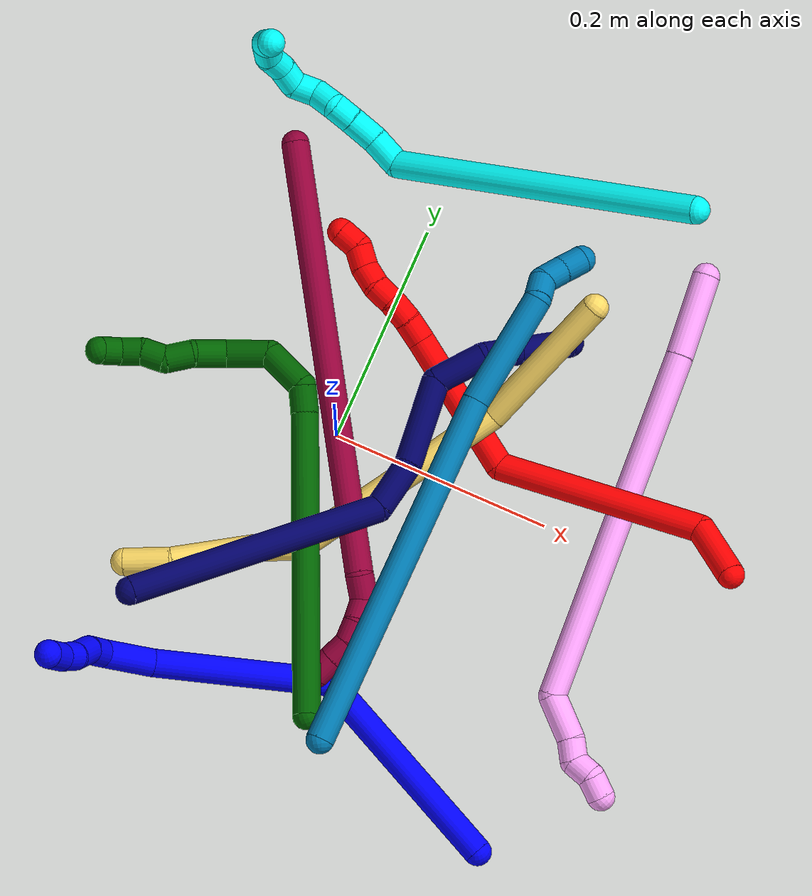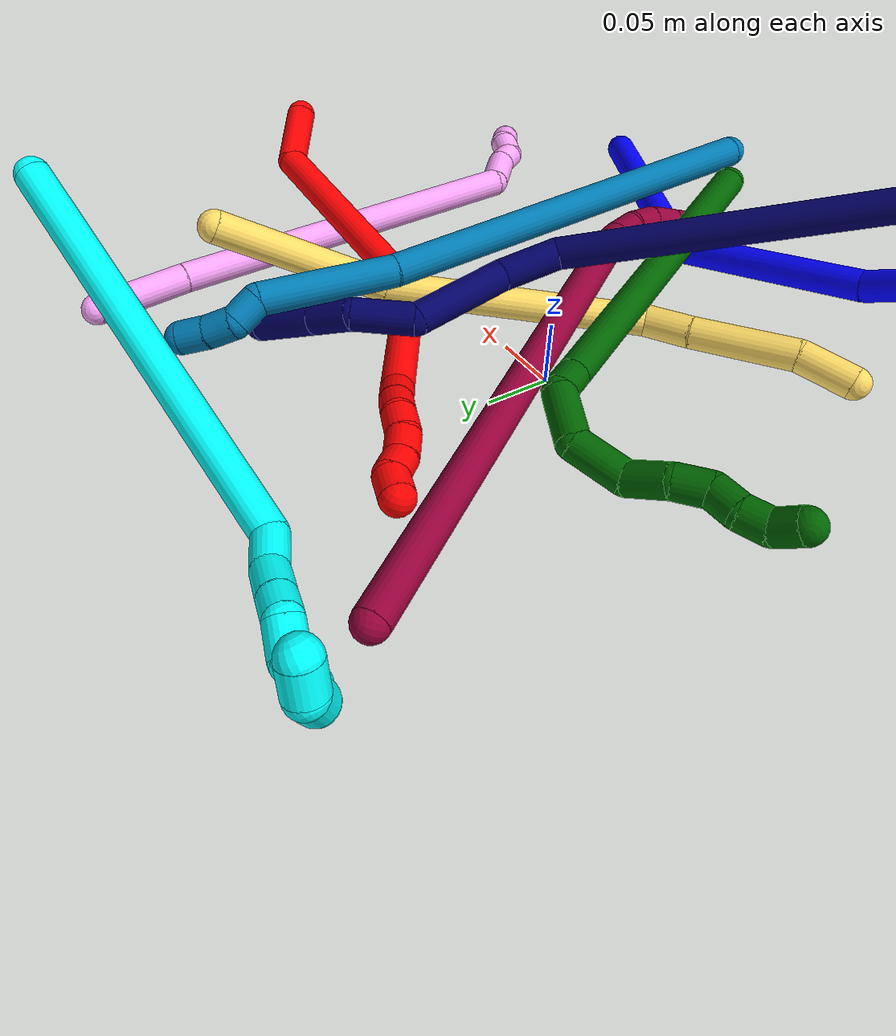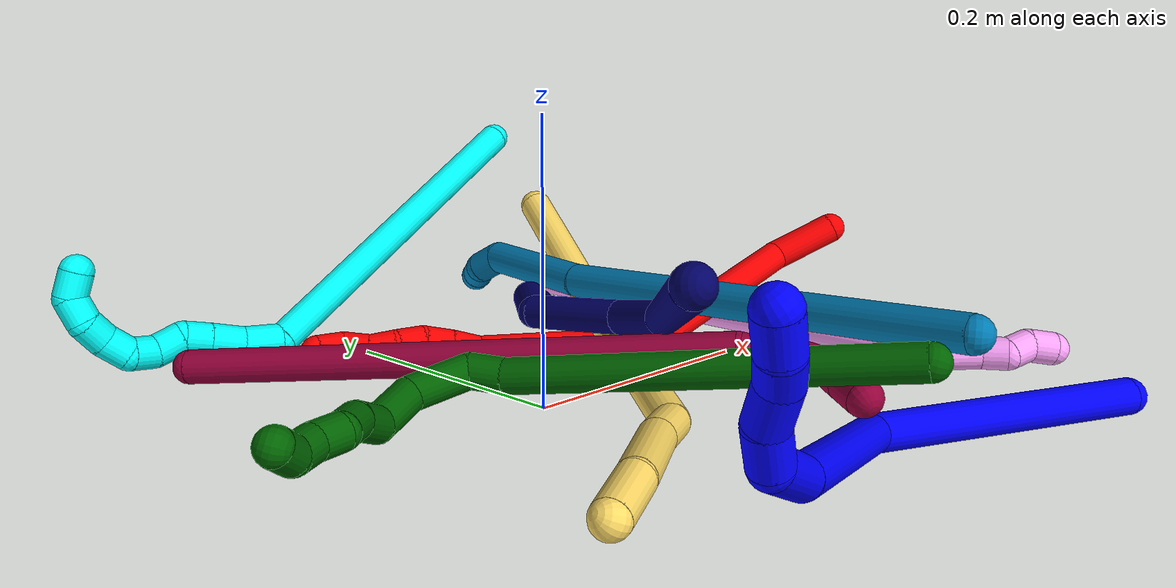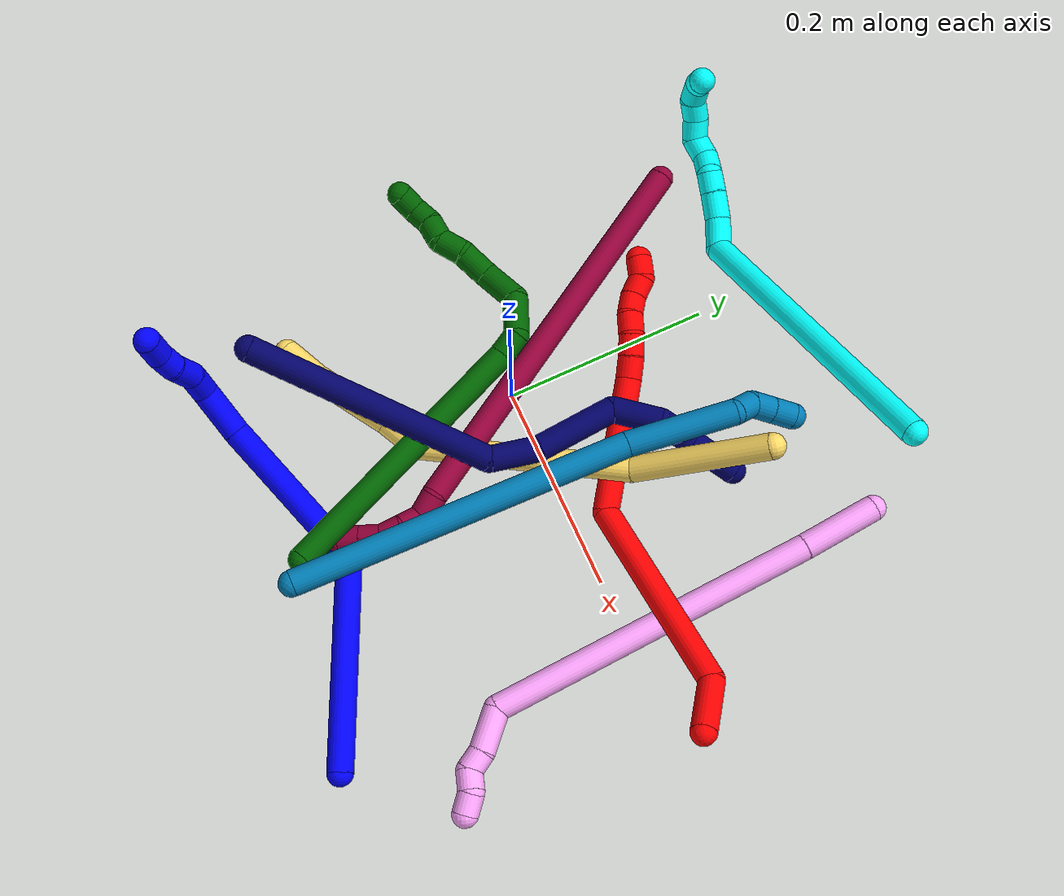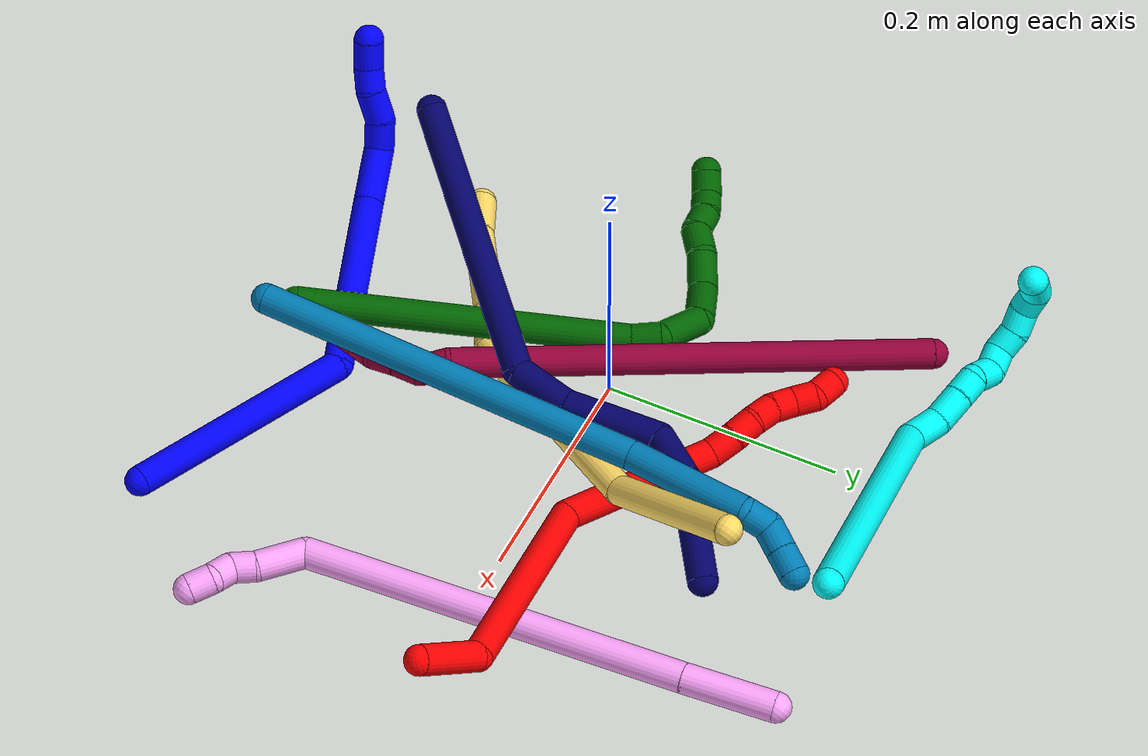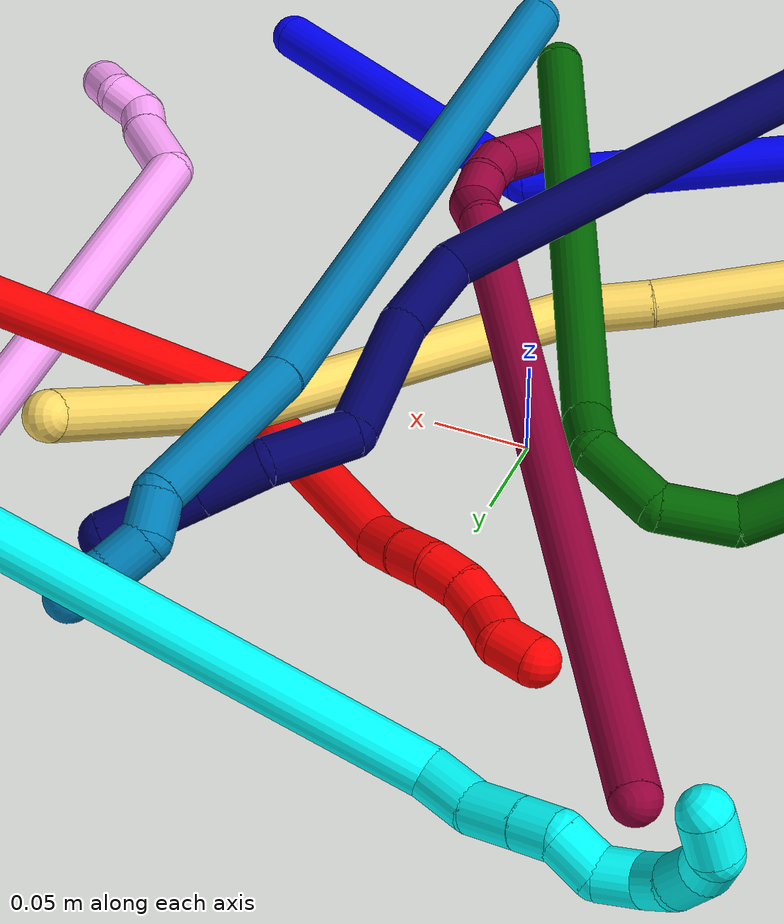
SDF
<sdf version="1.7">
 <world name="default">
  <plugin name="TubeGeneratorPlugin" filename="libtube_generator_plugin.so"/>
  <model name="photoneo_s_sensor">
   <static>1</static>
   <pose>0 0 2 1.57079 1.57079 3.14159</pose>
   <link name="link">
    <inertial><mass>0.1</mass></inertial>
    <sensor name="sensor" type="depth">
     <update_rate>30</update_rate>
     <camera>
      <horizontal_fov>1.22</horizontal_fov>
      <image><width>1920</width><height>1200</height><format>B8G8R8</format></image>
      <clip><near>0.1</near><far>4</far></clip>
      <depth_camera><output>points</output></depth_camera>
     </camera>
     <plugin name="camera_plugin" filename="libgazebo_ros_depth_camera.so">
      <baseline>0.2</baseline>
      <alwaysOn>1</alwaysOn>
      <updateRate>0.0</updateRate>
      <cameraName>camera_ir</cameraName>
      <imageTopicName>/camera/color/image_raw</imageTopicName>
      <cameraInfoTopicName>/camera/color/camera_info</cameraInfoTopicName>
      <depthImageTopicName>/camera/depth/image_raw</depthImageTopicName>
      <depthImageCameraInfoTopicName>/camera/depth/camera_info</depthImageCameraInfoTopicName>
      <pointCloudTopicName>/camera/depth/points</pointCloudTopicName>
      <frameName>fr_optical</frameName>
      <pointCloudCutoff>0.1</pointCloudCutoff>
      <pointCloudCutoffMax>2.0</pointCloudCutoffMax>
      <distortionK1>0</distortionK1>
      <distortionK2>0</distortionK2>
      <distortionK3>0</distortionK3>
      <distortionT1>0</distortionT1>
      <distortionT2>0</distortionT2>
      <CxPrime>0</CxPrime>
      <Cx>0</Cx>
      <Cy>0</Cy>
      <focalLength>0</focalLength>
      <hackBaseline>0</hackBaseline>
     </plugin>
    </sensor>
   </link>
  </model>
  <gravity>0 0 -9.8</gravity>
  <magnetic_field>6e-06 2.3e-05 -4.2e-05</magnetic_field>
  <atmosphere type="adiabatic"/>
  <physics name="default_physics" default="0" type="ode">
   <max_step_size>0.003</max_step_size>
   <real_time_factor>1</real_time_factor>
   <real_time_update_rate>1000</real_time_update_rate>
   <max_contacts>10000</max_contacts>
   <ode>
    <solver>
     <type>quick</type>
     <iters>100</iters>
     <sor>1.3</sor>
     <use_dynamic_moi_rescaling>0</use_dynamic_moi_rescaling>
    </solver>
    <constraints>
     <contact_max_correcting_vel>0</contact_max_correcting_vel>
     <contact_surface_layer>0.001</contact_surface_layer>
     <cfm>0</cfm>
     <erp>0.2</erp>
    </constraints>
   </ode>
  </physics>
  <scene><ambient>0.4 0.4 0.4 1</ambient><background>0.7 0.7 0.7 1</background><shadows>0</shadows></scene>
  <audio><device>default</device></audio>
  <spherical_coordinates>
   <surface_model>EARTH_WGS84</surface_model>
   <latitude_deg>0</latitude_deg>
   <longitude_deg>0</longitude_deg>
   <elevation>0</elevation>
   <heading_deg>0</heading_deg>
  </spherical_coordinates>
  <model name="bin">
   <static>1</static>
   <link name="bottom">
    <collision name="collision-bottom">
     <pose>0 0 -0.01 0 -0 0</pose>
     <geometry><box><size>0.8 0.6 0.02</size></box></geometry>
     <surface>
      <friction><ode><mu>100</mu><mu2>100</mu2></ode></friction>
      <contact><collide_bitmask>65535</collide_bitmask></contact>
     </surface>
    </collision>
   </link>
   <link name="west_wall">
    <collision name="collision-west_wall">
     <pose>-0.41 0 0.1 0 -0 0</pose>
     <geometry><box><size>0.02 0.6 0.2</size></box></geometry>
     <surface>
      <friction><ode><mu>100</mu><mu2>100</mu2></ode></friction>
      <contact><collide_bitmask>65535</collide_bitmask></contact>
     </surface>
    </collision>
   </link>
   <link name="east_wall">
    <collision name="collision-east_wall">
     <pose>0.41 0 0.1 0 -0 0</pose>
     <geometry><box><size>0.02 0.6 0.2</size></box></geometry>
     <surface>
      <friction><ode><mu>100</mu><mu2>100</mu2></ode></friction>
      <contact><collide_bitmask>65535</collide_bitmask></contact>
     </surface>
    </collision>
   </link>
   <link name="south_wall">
    <collision name="collision-south_wall">
     <pose>0 -0.31 0.1 0 -0 0</pose>
     <geometry><box><size>0.8 0.02 0.2</size></box></geometry>
     <surface>
      <friction><ode><mu>100</mu><mu2>100</mu2></ode></friction>
      <contact><collide_bitmask>65535</collide_bitmask></contact>
     </surface>
    </collision>
   </link>
   <link name="north_wall">
    <collision name="collision-north_wall">
     <pose>0 0.31 0.1 0 -0 0</pose>
     <geometry><box><size>0.8 0.02 0.2</size></box></geometry>
     <surface>
      <friction><ode><mu>100</mu><mu2>100</mu2></ode></friction>
      <contact><collide_bitmask>65535</collide_bitmask></contact>
     </surface>
    </collision>
   </link>
  </model>
  <model name="1">
   <static>0</static>
   <link name="1">
    <collision name="collision-cylinder-e_1_1_4">
     <pose>-0.064072 -0.057034 -0.048893 2.27949 -0.706175 -1.35112</pose>
     <geometry><cylinder><radius>0.0125</radius><length>0.197469</length></cylinder></geometry>
     <surface>
      <friction><ode><mu>1.16</mu><mu2>1.16</mu2><slip1>0</slip1><slip2>0</slip2></ode></friction>
      <contact><ode><kp>1e+06</kp><kd>1</kd><max_vel>0</max_vel><min_depth>0.001</min_depth></ode></contact>
     </surface>
    </collision>
    <visual name="visual-cylinder-e_1_1_4">
     <pose>-0.064072 -0.057034 -0.048893 2.27949 -0.706175 -1.35112</pose>
     <geometry><cylinder><radius>0.0125</radius><length>0.197469</length></cylinder></geometry>
     <material><ambient>0 0 1 1</ambient></material>
    </visual>
    <collision name="collision-cylinder-e_2_4_5">
     <pose>-0.201116 -0.10507 -0.126527 -2.83821 -1.17938 2.69237</pose>
     <geometry><cylinder><radius>0.0125</radius><length>0.157886</length></cylinder></geometry>
     <surface>
      <friction><ode><mu>1.16</mu><mu2>1.16</mu2><slip1>0</slip1><slip2>0</slip2></ode></friction>
      <contact><ode><kp>1e+06</kp><kd>1</kd><max_vel>0</max_vel><min_depth>0.001</min_depth></ode></contact>
     </surface>
    </collision>
    <visual name="visual-cylinder-e_2_4_5">
     <pose>-0.201116 -0.10507 -0.126527 -2.83821 -1.17938 2.69237</pose>
     <geometry><cylinder><radius>0.0125</radius><length>0.157886</length></cylinder></geometry>
     <material><ambient>0 0 1 1</ambient></material>
    </visual>
    <collision name="collision-cylinder-e_3_5_6">
     <pose>-0.292778 -0.091359 -0.169377 -2.81919 -0.898559 2.49104</pose>
     <geometry><cylinder><radius>0.0125</radius><length>0.047774</length></cylinder></geometry>
     <surface>
      <friction><ode><mu>1.16</mu><mu2>1.16</mu2><slip1>0</slip1><slip2>0</slip2></ode></friction>
      <contact><ode><kp>1e+06</kp><kd>1</kd><max_vel>0</max_vel><min_depth>0.001</min_depth></ode></contact>
     </surface>
    </collision>
    <visual name="visual-cylinder-e_3_5_6">
     <pose>-0.292778 -0.091359 -0.169377 -2.81919 -0.898559 2.49104</pose>
     <geometry><cylinder><radius>0.0125</radius><length>0.047774</length></cylinder></geometry>
     <material><ambient>0 0 1 1</ambient></material>
    </visual>
    <collision name="collision-cylinder-e_4_6_7">
     <pose>-0.314172 -0.080437 -0.194652 -2.63411 -0.208548 0.76713</pose>
     <geometry><cylinder><radius>0.0125</radius><length>0.026118</length></cylinder></geometry>
     <surface>
      <friction><ode><mu>1.16</mu><mu2>1.16</mu2><slip1>0</slip1><slip2>0</slip2></ode></friction>
      <contact><ode><kp>1e+06</kp><kd>1</kd><max_vel>0</max_vel><min_depth>0.001</min_depth></ode></contact>
     </surface>
    </collision>
    <visual name="visual-cylinder-e_4_6_7">
     <pose>-0.314172 -0.080437 -0.194652 -2.63411 -0.208548 0.76713</pose>
     <geometry><cylinder><radius>0.0125</radius><length>0.026118</length></cylinder></geometry>
     <material><ambient>0 0 1 1</ambient></material>
    </visual>
    <collision name="collision-cylinder-e_5_7_8">
     <pose>-0.319135 -0.064406 -0.214731 -2.30774 -0.168702 0.377279</pose>
     <geometry><cylinder><radius>0.0125</radius><length>0.026908</length></cylinder></geometry>
     <surface>
      <friction><ode><mu>1.16</mu><mu2>1.16</mu2><slip1>0</slip1><slip2>0</slip2></ode></friction>
      <contact><ode><kp>1e+06</kp><kd>1</kd><max_vel>0</max_vel><min_depth>0.001</min_depth></ode></contact>
     </surface>
    </collision>
    <visual name="visual-cylinder-e_5_7_8">
     <pose>-0.319135 -0.064406 -0.214731 -2.30774 -0.168702 0.377279</pose>
     <geometry><cylinder><radius>0.0125</radius><length>0.026908</length></cylinder></geometry>
     <material><ambient>0 0 1 1</ambient></material>
    </visual>
    <collision name="collision-cylinder-e_6_8_9">
     <pose>-0.325061 -0.048916 -0.231051 -2.48828 -0.37465 1.02019</pose>
     <geometry><cylinder><radius>0.0125</radius><length>0.020045</length></cylinder></geometry>
     <surface>
      <friction><ode><mu>1.16</mu><mu2>1.16</mu2><slip1>0</slip1><slip2>0</slip2></ode></friction>
      <contact><ode><kp>1e+06</kp><kd>1</kd><max_vel>0</max_vel><min_depth>0.001</min_depth></ode></contact>
     </surface>
    </collision>
    <visual name="visual-cylinder-e_6_8_9">
     <pose>-0.325061 -0.048916 -0.231051 -2.48828 -0.37465 1.02019</pose>
     <geometry><cylinder><radius>0.0125</radius><length>0.020045</length></cylinder></geometry>
     <material><ambient>0 0 1 1</ambient></material>
    </visual>
    <collision name="collision-cylinder-e_7_9_2">
     <pose>-0.330977 -0.037385 -0.248567 -2.61618 -0.19006 0.681247</pose>
     <geometry><cylinder><radius>0.0125</radius><length>0.0238</length></cylinder></geometry>
     <surface>
      <friction><ode><mu>1.16</mu><mu2>1.16</mu2><slip1>0</slip1><slip2>0</slip2></ode></friction>
      <contact><ode><kp>1e+06</kp><kd>1</kd><max_vel>0</max_vel><min_depth>0.001</min_depth></ode></contact>
     </surface>
    </collision>
    <visual name="visual-cylinder-e_7_9_2">
     <pose>-0.330977 -0.037385 -0.248567 -2.61618 -0.19006 0.681247</pose>
     <geometry><cylinder><radius>0.0125</radius><length>0.0238</length></cylinder></geometry>
     <material><ambient>0 0 1 1</ambient></material>
    </visual>
    <collision name="collision-sphere-2">
     <pose>-0.333225 -0.031524 -0.258676 0 -0 0</pose>
     <geometry><sphere><radius>0.0125</radius></sphere></geometry>
     <surface>
      <friction><ode><mu>1.16</mu><mu2>1.16</mu2><slip1>0</slip1><slip2>0</slip2></ode></friction>
      <contact><ode><kp>1e+06</kp><kd>1</kd><max_vel>0</max_vel><min_depth>0.001</min_depth></ode></contact>
     </surface>
    </collision>
    <visual name="visual-sphere-2">
     <pose>-0.333225 -0.031524 -0.258676 0 -0 0</pose>
     <geometry><sphere><radius>0.0125</radius></sphere></geometry>
     <material><ambient>0 0 1 1</ambient></material>
    </visual>
    <collision name="collision-sphere-9">
     <pose>-0.328729 -0.043246 -0.238457 0 -0 0</pose>
     <geometry><sphere><radius>0.0125</radius></sphere></geometry>
     <surface>
      <friction><ode><mu>1.16</mu><mu2>1.16</mu2><slip1>0</slip1><slip2>0</slip2></ode></friction>
      <contact><ode><kp>1e+06</kp><kd>1</kd><max_vel>0</max_vel><min_depth>0.001</min_depth></ode></contact>
     </surface>
    </collision>
    <visual name="visual-sphere-9">
     <pose>-0.328729 -0.043246 -0.238457 0 -0 0</pose>
     <geometry><sphere><radius>0.0125</radius></sphere></geometry>
     <material><ambient>0 0 1 1</ambient></material>
    </visual>
    <collision name="collision-sphere-4">
     <pose>-0.128143 -0.114067 -0.097786 0 -0 0</pose>
     <geometry><sphere><radius>0.0125</radius></sphere></geometry>
     <surface>
      <friction><ode><mu>1.16</mu><mu2>1.16</mu2><slip1>0</slip1><slip2>0</slip2></ode></friction>
      <contact><ode><kp>1e+06</kp><kd>1</kd><max_vel>0</max_vel><min_depth>0.001</min_depth></ode></contact>
     </surface>
    </collision>
    <visual name="visual-sphere-4">
     <pose>-0.128143 -0.114067 -0.097786 0 -0 0</pose>
     <geometry><sphere><radius>0.0125</radius></sphere></geometry>
     <material><ambient>0 0 1 1</ambient></material>
    </visual>
    <collision name="collision-sphere-1">
     <geometry><sphere><radius>0.0125</radius></sphere></geometry>
     <surface>
      <friction><ode><mu>1.16</mu><mu2>1.16</mu2><slip1>0</slip1><slip2>0</slip2></ode></friction>
      <contact><ode><kp>1e+06</kp><kd>1</kd><max_vel>0</max_vel><min_depth>0.001</min_depth></ode></contact>
     </surface>
    </collision>
    <visual name="visual-sphere-1">
     <geometry><sphere><radius>0.0125</radius></sphere></geometry>
     <material><ambient>0 0 1 1</ambient></material>
    </visual>
    <collision name="collision-sphere-8">
     <pose>-0.321394 -0.054585 -0.223644 0 -0 0</pose>
     <geometry><sphere><radius>0.0125</radius></sphere></geometry>
     <surface>
      <friction><ode><mu>1.16</mu><mu2>1.16</mu2><slip1>0</slip1><slip2>0</slip2></ode></friction>
      <contact><ode><kp>1e+06</kp><kd>1</kd><max_vel>0</max_vel><min_depth>0.001</min_depth></ode></contact>
     </surface>
    </collision>
    <visual name="visual-sphere-8">
     <pose>-0.321394 -0.054585 -0.223644 0 -0 0</pose>
     <geometry><sphere><radius>0.0125</radius></sphere></geometry>
     <material><ambient>0 0 1 1</ambient></material>
    </visual>
    <collision name="collision-sphere-5">
     <pose>-0.274088 -0.096072 -0.155268 0 -0 0</pose>
     <geometry><sphere><radius>0.0125</radius></sphere></geometry>
     <surface>
      <friction><ode><mu>1.16</mu><mu2>1.16</mu2><slip1>0</slip1><slip2>0</slip2></ode></friction>
      <contact><ode><kp>1e+06</kp><kd>1</kd><max_vel>0</max_vel><min_depth>0.001</min_depth></ode></contact>
     </surface>
    </collision>
    <visual name="visual-sphere-5">
     <pose>-0.274088 -0.096072 -0.155268 0 -0 0</pose>
     <geometry><sphere><radius>0.0125</radius></sphere></geometry>
     <material><ambient>0 0 1 1</ambient></material>
    </visual>
    <collision name="collision-sphere-6">
     <pose>-0.311468 -0.086646 -0.183486 0 -0 0</pose>
     <geometry><sphere><radius>0.0125</radius></sphere></geometry>
     <surface>
      <friction><ode><mu>1.16</mu><mu2>1.16</mu2><slip1>0</slip1><slip2>0</slip2></ode></friction>
      <contact><ode><kp>1e+06</kp><kd>1</kd><max_vel>0</max_vel><min_depth>0.001</min_depth></ode></contact>
     </surface>
    </collision>
    <visual name="visual-sphere-6">
     <pose>-0.311468 -0.086646 -0.183486 0 -0 0</pose>
     <geometry><sphere><radius>0.0125</radius></sphere></geometry>
     <material><ambient>0 0 1 1</ambient></material>
    </visual>
    <collision name="collision-sphere-7">
     <pose>-0.316876 -0.074228 -0.205818 0 -0 0</pose>
     <geometry><sphere><radius>0.0125</radius></sphere></geometry>
     <surface>
      <friction><ode><mu>1.16</mu><mu2>1.16</mu2><slip1>0</slip1><slip2>0</slip2></ode></friction>
      <contact><ode><kp>1e+06</kp><kd>1</kd><max_vel>0</max_vel><min_depth>0.001</min_depth></ode></contact>
     </surface>
    </collision>
    <visual name="visual-sphere-7">
     <pose>-0.316876 -0.074228 -0.205818 0 -0 0</pose>
     <geometry><sphere><radius>0.0125</radius></sphere></geometry>
     <material><ambient>0 0 1 1</ambient></material>
    </visual>
    <inertial>
     <pose>-0.179157 -0.07584 -0.118265 0 -0 0</pose>
     <mass>0.5</mass>
     <inertia>
      <ixx>-0.00045</ixx>
      <ixy>0</ixy>
      <ixz>0</ixz>
      <iyy>0.000133</iyy>
      <iyz>0</iyz>
      <izz>0.00105</izz>
     </inertia>
    </inertial>
   </link>
   <pose>0.261727 -0.288501 0.01365 2.60643 -0.216207 0.406193</pose>
  </model>
  <model name="2">
   <static>0</static>
   <link name="2">
    <collision name="collision-cylinder-e_1_1_4">
     <pose>-0.008098 0.021891 0.014221 -0.994659 -0.300814 0.164167</pose>
     <geometry><cylinder><radius>0.0125</radius><length>0.054664</length></cylinder></geometry>
     <surface>
      <friction><ode><mu>1.16</mu><mu2>1.16</mu2><slip1>0</slip1><slip2>0</slip2></ode></friction>
      <contact><ode><kp>1e+06</kp><kd>1</kd><max_vel>0</max_vel><min_depth>0.001</min_depth></ode></contact>
     </surface>
    </collision>
    <visual name="visual-cylinder-e_1_1_4">
     <pose>-0.008098 0.021891 0.014221 -0.994659 -0.300814 0.164167</pose>
     <geometry><cylinder><radius>0.0125</radius><length>0.054664</length></cylinder></geometry>
     <material><ambient>1 0 0 1</ambient></material>
    </visual>
    <collision name="collision-cylinder-e_2_4_5">
     <pose>0.007149 0.135197 0.037736 -1.46949 0.248808 -0.225011</pose>
     <geometry><cylinder><radius>0.0125</radius><length>0.189613</length></cylinder></geometry>
     <surface>
      <friction><ode><mu>1.16</mu><mu2>1.16</mu2><slip1>0</slip1><slip2>0</slip2></ode></friction>
      <contact><ode><kp>1e+06</kp><kd>1</kd><max_vel>0</max_vel><min_depth>0.001</min_depth></ode></contact>
     </surface>
    </collision>
    <visual name="visual-cylinder-e_2_4_5">
     <pose>0.007149 0.135197 0.037736 -1.46949 0.248808 -0.225011</pose>
     <geometry><cylinder><radius>0.0125</radius><length>0.189613</length></cylinder></geometry>
     <material><ambient>1 0 0 1</ambient></material>
    </visual>
    <collision name="collision-cylinder-e_3_5_6">
     <pose>0.000947 0.285188 0.054882 -1.43752 -0.463627 0.407317</pose>
     <geometry><cylinder><radius>0.0125</radius><length>0.132148</length></cylinder></geometry>
     <surface>
      <friction><ode><mu>1.16</mu><mu2>1.16</mu2><slip1>0</slip1><slip2>0</slip2></ode></friction>
      <contact><ode><kp>1e+06</kp><kd>1</kd><max_vel>0</max_vel><min_depth>0.001</min_depth></ode></contact>
     </surface>
    </collision>
    <visual name="visual-cylinder-e_3_5_6">
     <pose>0.000947 0.285188 0.054882 -1.43752 -0.463627 0.407317</pose>
     <geometry><cylinder><radius>0.0125</radius><length>0.132148</length></cylinder></geometry>
     <material><ambient>1 0 0 1</ambient></material>
    </visual>
    <collision name="collision-cylinder-e_4_6_7">
     <pose>-0.034038 0.353492 0.06074 -1.77302 -0.500904 0.607766</pose>
     <geometry><cylinder><radius>0.0125</radius><length>0.022644</length></cylinder></geometry>
     <surface>
      <friction><ode><mu>1.16</mu><mu2>1.16</mu2><slip1>0</slip1><slip2>0</slip2></ode></friction>
      <contact><ode><kp>1e+06</kp><kd>1</kd><max_vel>0</max_vel><min_depth>0.001</min_depth></ode></contact>
     </surface>
    </collision>
    <visual name="visual-cylinder-e_4_6_7">
     <pose>-0.034038 0.353492 0.06074 -1.77302 -0.500904 0.607766</pose>
     <geometry><cylinder><radius>0.0125</radius><length>0.022644</length></cylinder></geometry>
     <material><ambient>1 0 0 1</ambient></material>
    </visual>
    <collision name="collision-cylinder-e_5_7_8">
     <pose>-0.043386 0.372753 0.057099 -1.74176 -0.384225 0.453983</pose>
     <geometry><cylinder><radius>0.0125</radius><length>0.020868</length></cylinder></geometry>
     <surface>
      <friction><ode><mu>1.16</mu><mu2>1.16</mu2><slip1>0</slip1><slip2>0</slip2></ode></friction>
      <contact><ode><kp>1e+06</kp><kd>1</kd><max_vel>0</max_vel><min_depth>0.001</min_depth></ode></contact>
     </surface>
    </collision>
    <visual name="visual-cylinder-e_5_7_8">
     <pose>-0.043386 0.372753 0.057099 -1.74176 -0.384225 0.453983</pose>
     <geometry><cylinder><radius>0.0125</radius><length>0.020868</length></cylinder></geometry>
     <material><ambient>1 0 0 1</ambient></material>
    </visual>
    <collision name="collision-cylinder-e_6_8_9">
     <pose>-0.049531 0.392024 0.056216 -1.49264 -0.224771 0.207984</pose>
     <geometry><cylinder><radius>0.0125</radius><length>0.020041</length></cylinder></geometry>
     <surface>
      <friction><ode><mu>1.16</mu><mu2>1.16</mu2><slip1>0</slip1><slip2>0</slip2></ode></friction>
      <contact><ode><kp>1e+06</kp><kd>1</kd><max_vel>0</max_vel><min_depth>0.001</min_depth></ode></contact>
     </surface>
    </collision>
    <visual name="visual-cylinder-e_6_8_9">
     <pose>-0.049531 0.392024 0.056216 -1.49264 -0.224771 0.207984</pose>
     <geometry><cylinder><radius>0.0125</radius><length>0.020041</length></cylinder></geometry>
     <material><ambient>1 0 0 1</ambient></material>
    </visual>
    <collision name="collision-cylinder-e_7_9_10">
     <pose>-0.055814 0.410539 0.05956 -1.28482 -0.416778 0.313866</pose>
     <geometry><cylinder><radius>0.0125</radius><length>0.020009</length></cylinder></geometry>
     <surface>
      <friction><ode><mu>1.16</mu><mu2>1.16</mu2><slip1>0</slip1><slip2>0</slip2></ode></friction>
      <contact><ode><kp>1e+06</kp><kd>1</kd><max_vel>0</max_vel><min_depth>0.001</min_depth></ode></contact>
     </surface>
    </collision>
    <visual name="visual-cylinder-e_7_9_10">
     <pose>-0.055814 0.410539 0.05956 -1.28482 -0.416778 0.313866</pose>
     <geometry><cylinder><radius>0.0125</radius><length>0.020009</length></cylinder></geometry>
     <material><ambient>1 0 0 1</ambient></material>
    </visual>
    <collision name="collision-cylinder-e_8_10_11">
     <pose>-0.066589 0.426646 0.063191 -1.42843 -0.737224 0.646229</pose>
     <geometry><cylinder><radius>0.0125</radius><length>0.020007</length></cylinder></geometry>
     <surface>
      <friction><ode><mu>1.16</mu><mu2>1.16</mu2><slip1>0</slip1><slip2>0</slip2></ode></friction>
      <contact><ode><kp>1e+06</kp><kd>1</kd><max_vel>0</max_vel><min_depth>0.001</min_depth></ode></contact>
     </surface>
    </collision>
    <visual name="visual-cylinder-e_8_10_11">
     <pose>-0.066589 0.426646 0.063191 -1.42843 -0.737224 0.646229</pose>
     <geometry><cylinder><radius>0.0125</radius><length>0.020007</length></cylinder></geometry>
     <material><ambient>1 0 0 1</ambient></material>
    </visual>
    <collision name="collision-cylinder-e_9_11_2">
     <pose>-0.075129 0.443809 0.064566 -1.53779 -0.182504 0.176609</pose>
     <geometry><cylinder><radius>0.0125</radius><length>0.020006</length></cylinder></geometry>
     <surface>
      <friction><ode><mu>1.16</mu><mu2>1.16</mu2><slip1>0</slip1><slip2>0</slip2></ode></friction>
      <contact><ode><kp>1e+06</kp><kd>1</kd><max_vel>0</max_vel><min_depth>0.001</min_depth></ode></contact>
     </surface>
    </collision>
    <visual name="visual-cylinder-e_9_11_2">
     <pose>-0.075129 0.443809 0.064566 -1.53779 -0.182504 0.176609</pose>
     <geometry><cylinder><radius>0.0125</radius><length>0.020006</length></cylinder></geometry>
     <material><ambient>1 0 0 1</ambient></material>
    </visual>
    <collision name="collision-sphere-2">
     <pose>-0.076944 0.45364 0.064891 0 -0 0</pose>
     <geometry><sphere><radius>0.0125</radius></sphere></geometry>
     <surface>
      <friction><ode><mu>1.16</mu><mu2>1.16</mu2><slip1>0</slip1><slip2>0</slip2></ode></friction>
      <contact><ode><kp>1e+06</kp><kd>1</kd><max_vel>0</max_vel><min_depth>0.001</min_depth></ode></contact>
     </surface>
    </collision>
    <visual name="visual-sphere-2">
     <pose>-0.076944 0.45364 0.064891 0 -0 0</pose>
     <geometry><sphere><radius>0.0125</radius></sphere></geometry>
     <material><ambient>1 0 0 1</ambient></material>
    </visual>
    <collision name="collision-sphere-11">
     <pose>-0.073313 0.433977 0.064242 0 -0 0</pose>
     <geometry><sphere><radius>0.0125</radius></sphere></geometry>
     <surface>
      <friction><ode><mu>1.16</mu><mu2>1.16</mu2><slip1>0</slip1><slip2>0</slip2></ode></friction>
      <contact><ode><kp>1e+06</kp><kd>1</kd><max_vel>0</max_vel><min_depth>0.001</min_depth></ode></contact>
     </surface>
    </collision>
    <visual name="visual-sphere-11">
     <pose>-0.073313 0.433977 0.064242 0 -0 0</pose>
     <geometry><sphere><radius>0.0125</radius></sphere></geometry>
     <material><ambient>1 0 0 1</ambient></material>
    </visual>
    <collision name="collision-sphere-10">
     <pose>-0.059864 0.419315 0.06214 0 -0 0</pose>
     <geometry><sphere><radius>0.0125</radius></sphere></geometry>
     <surface>
      <friction><ode><mu>1.16</mu><mu2>1.16</mu2><slip1>0</slip1><slip2>0</slip2></ode></friction>
      <contact><ode><kp>1e+06</kp><kd>1</kd><max_vel>0</max_vel><min_depth>0.001</min_depth></ode></contact>
     </surface>
    </collision>
    <visual name="visual-sphere-10">
     <pose>-0.059864 0.419315 0.06214 0 -0 0</pose>
     <geometry><sphere><radius>0.0125</radius></sphere></geometry>
     <material><ambient>1 0 0 1</ambient></material>
    </visual>
    <collision name="collision-sphere-9">
     <pose>-0.051764 0.401762 0.056979 0 -0 0</pose>
     <geometry><sphere><radius>0.0125</radius></sphere></geometry>
     <surface>
      <friction><ode><mu>1.16</mu><mu2>1.16</mu2><slip1>0</slip1><slip2>0</slip2></ode></friction>
      <contact><ode><kp>1e+06</kp><kd>1</kd><max_vel>0</max_vel><min_depth>0.001</min_depth></ode></contact>
     </surface>
    </collision>
    <visual name="visual-sphere-9">
     <pose>-0.051764 0.401762 0.056979 0 -0 0</pose>
     <geometry><sphere><radius>0.0125</radius></sphere></geometry>
     <material><ambient>1 0 0 1</ambient></material>
    </visual>
    <collision name="collision-sphere-4">
     <pose>-0.016197 0.043781 0.028443 0 -0 0</pose>
     <geometry><sphere><radius>0.0125</radius></sphere></geometry>
     <surface>
      <friction><ode><mu>1.16</mu><mu2>1.16</mu2><slip1>0</slip1><slip2>0</slip2></ode></friction>
      <contact><ode><kp>1e+06</kp><kd>1</kd><max_vel>0</max_vel><min_depth>0.001</min_depth></ode></contact>
     </surface>
    </collision>
    <visual name="visual-sphere-4">
     <pose>-0.016197 0.043781 0.028443 0 -0 0</pose>
     <geometry><sphere><radius>0.0125</radius></sphere></geometry>
     <material><ambient>1 0 0 1</ambient></material>
    </visual>
    <collision name="collision-sphere-1">
     <geometry><sphere><radius>0.0125</radius></sphere></geometry>
     <surface>
      <friction><ode><mu>1.16</mu><mu2>1.16</mu2><slip1>0</slip1><slip2>0</slip2></ode></friction>
      <contact><ode><kp>1e+06</kp><kd>1</kd><max_vel>0</max_vel><min_depth>0.001</min_depth></ode></contact>
     </surface>
    </collision>
    <visual name="visual-sphere-1">
     <geometry><sphere><radius>0.0125</radius></sphere></geometry>
     <material><ambient>1 0 0 1</ambient></material>
    </visual>
    <collision name="collision-sphere-8">
     <pose>-0.047297 0.382285 0.055454 0 -0 0</pose>
     <geometry><sphere><radius>0.0125</radius></sphere></geometry>
     <surface>
      <friction><ode><mu>1.16</mu><mu2>1.16</mu2><slip1>0</slip1><slip2>0</slip2></ode></friction>
      <contact><ode><kp>1e+06</kp><kd>1</kd><max_vel>0</max_vel><min_depth>0.001</min_depth></ode></contact>
     </surface>
    </collision>
    <visual name="visual-sphere-8">
     <pose>-0.047297 0.382285 0.055454 0 -0 0</pose>
     <geometry><sphere><radius>0.0125</radius></sphere></geometry>
     <material><ambient>1 0 0 1</ambient></material>
    </visual>
    <collision name="collision-sphere-5">
     <pose>0.030495 0.226613 0.047029 0 -0 0</pose>
     <geometry><sphere><radius>0.0125</radius></sphere></geometry>
     <surface>
      <friction><ode><mu>1.16</mu><mu2>1.16</mu2><slip1>0</slip1><slip2>0</slip2></ode></friction>
      <contact><ode><kp>1e+06</kp><kd>1</kd><max_vel>0</max_vel><min_depth>0.001</min_depth></ode></contact>
     </surface>
    </collision>
    <visual name="visual-sphere-5">
     <pose>0.030495 0.226613 0.047029 0 -0 0</pose>
     <geometry><sphere><radius>0.0125</radius></sphere></geometry>
     <material><ambient>1 0 0 1</ambient></material>
    </visual>
    <collision name="collision-sphere-6">
     <pose>-0.028601 0.343763 0.062735 0 -0 0</pose>
     <geometry><sphere><radius>0.0125</radius></sphere></geometry>
     <surface>
      <friction><ode><mu>1.16</mu><mu2>1.16</mu2><slip1>0</slip1><slip2>0</slip2></ode></friction>
      <contact><ode><kp>1e+06</kp><kd>1</kd><max_vel>0</max_vel><min_depth>0.001</min_depth></ode></contact>
     </surface>
    </collision>
    <visual name="visual-sphere-6">
     <pose>-0.028601 0.343763 0.062735 0 -0 0</pose>
     <geometry><sphere><radius>0.0125</radius></sphere></geometry>
     <material><ambient>1 0 0 1</ambient></material>
    </visual>
    <collision name="collision-sphere-7">
     <pose>-0.039475 0.363221 0.058745 0 -0 0</pose>
     <geometry><sphere><radius>0.0125</radius></sphere></geometry>
     <surface>
      <friction><ode><mu>1.16</mu><mu2>1.16</mu2><slip1>0</slip1><slip2>0</slip2></ode></friction>
      <contact><ode><kp>1e+06</kp><kd>1</kd><max_vel>0</max_vel><min_depth>0.001</min_depth></ode></contact>
     </surface>
    </collision>
    <visual name="visual-sphere-7">
     <pose>-0.039475 0.363221 0.058745 0 -0 0</pose>
     <geometry><sphere><radius>0.0125</radius></sphere></geometry>
     <material><ambient>1 0 0 1</ambient></material>
    </visual>
    <inertial>
     <pose>-0.011166 0.227575 0.045253 0 -0 0</pose>
     <mass>0.5</mass>
     <inertia>
      <ixx>0.000673</ixx>
      <ixy>0</ixy>
      <ixz>0</ixz>
      <iyy>0.000144</iyy>
      <iyz>0</iyz>
      <izz>-0.000791</izz>
     </inertia>
    </inertial>
   </link>
   <pose>0.367554 0.017241 0.075658 -3.09843 0.328078 -1.68146</pose>
  </model>
  <model name="3">
   <static>0</static>
   <link name="3">
    <collision name="collision-cylinder-e_1_1_4">
     <pose>-0.024512 0.035489 0.142966 -0.243313 -0.164893 0.020205</pose>
     <geometry><cylinder><radius>0.0125</radius><length>0.298661</length></cylinder></geometry>
     <surface>
      <friction><ode><mu>1.16</mu><mu2>1.16</mu2><slip1>0</slip1><slip2>0</slip2></ode></friction>
      <contact><ode><kp>1e+06</kp><kd>1</kd><max_vel>0</max_vel><min_depth>0.001</min_depth></ode></contact>
     </surface>
    </collision>
    <visual name="visual-cylinder-e_1_1_4">
     <pose>-0.024512 0.035489 0.142966 -0.243313 -0.164893 0.020205</pose>
     <geometry><cylinder><radius>0.0125</radius><length>0.298661</length></cylinder></geometry>
     <material><ambient>0.003922 1 0.996078 1</ambient></material>
    </visual>
    <collision name="collision-cylinder-e_2_4_5">
     <pose>-0.060514 0.071444 0.295275 -0.049941 -0.887465 0.023743</pose>
     <geometry><cylinder><radius>0.0125</radius><length>0.029633</length></cylinder></geometry>
     <surface>
      <friction><ode><mu>1.16</mu><mu2>1.16</mu2><slip1>0</slip1><slip2>0</slip2></ode></friction>
      <contact><ode><kp>1e+06</kp><kd>1</kd><max_vel>0</max_vel><min_depth>0.001</min_depth></ode></contact>
     </surface>
    </collision>
    <visual name="visual-cylinder-e_2_4_5">
     <pose>-0.060514 0.071444 0.295275 -0.049941 -0.887465 0.023743</pose>
     <geometry><cylinder><radius>0.0125</radius><length>0.029633</length></cylinder></geometry>
     <material><ambient>0.003922 1 0.996078 1</ambient></material>
    </visual>
    <collision name="collision-cylinder-e_3_5_6">
     <pose>-0.083045 0.075877 0.311397 -0.529384 -0.952541 0.277859</pose>
     <geometry><cylinder><radius>0.0125</radius><length>0.027099</length></cylinder></geometry>
     <surface>
      <friction><ode><mu>1.16</mu><mu2>1.16</mu2><slip1>0</slip1><slip2>0</slip2></ode></friction>
      <contact><ode><kp>1e+06</kp><kd>1</kd><max_vel>0</max_vel><min_depth>0.001</min_depth></ode></contact>
     </surface>
    </collision>
    <visual name="visual-cylinder-e_3_5_6">
     <pose>-0.083045 0.075877 0.311397 -0.529384 -0.952541 0.277859</pose>
     <geometry><cylinder><radius>0.0125</radius><length>0.027099</length></cylinder></geometry>
     <material><ambient>0.003922 1 0.996078 1</ambient></material>
    </visual>
    <collision name="collision-cylinder-e_4_6_7">
     <pose>-0.102072 0.082806 0.323526 -0.505668 -0.917229 0.25375</pose>
     <geometry><cylinder><radius>0.0125</radius><length>0.020119</length></cylinder></geometry>
     <surface>
      <friction><ode><mu>1.16</mu><mu2>1.16</mu2><slip1>0</slip1><slip2>0</slip2></ode></friction>
      <contact><ode><kp>1e+06</kp><kd>1</kd><max_vel>0</max_vel><min_depth>0.001</min_depth></ode></contact>
     </surface>
    </collision>
    <visual name="visual-cylinder-e_4_6_7">
     <pose>-0.102072 0.082806 0.323526 -0.505668 -0.917229 0.25375</pose>
     <geometry><cylinder><radius>0.0125</radius><length>0.020119</length></cylinder></geometry>
     <material><ambient>0.003922 1 0.996078 1</ambient></material>
    </visual>
    <collision name="collision-cylinder-e_5_7_8">
     <pose>-0.115253 0.085155 0.338801 0.061755 -0.481385 -0.015162</pose>
     <geometry><cylinder><radius>0.0125</radius><length>0.022436</length></cylinder></geometry>
     <surface>
      <friction><ode><mu>1.16</mu><mu2>1.16</mu2><slip1>0</slip1><slip2>0</slip2></ode></friction>
      <contact><ode><kp>1e+06</kp><kd>1</kd><max_vel>0</max_vel><min_depth>0.001</min_depth></ode></contact>
     </surface>
    </collision>
    <visual name="visual-cylinder-e_5_7_8">
     <pose>-0.115253 0.085155 0.338801 0.061755 -0.481385 -0.015162</pose>
     <geometry><cylinder><radius>0.0125</radius><length>0.022436</length></cylinder></geometry>
     <material><ambient>0.003922 1 0.996078 1</ambient></material>
    </visual>
    <collision name="collision-cylinder-e_6_8_9">
     <pose>-0.126568 0.089966 0.355545 -0.671919 -0.61237 0.21989</pose>
     <geometry><cylinder><radius>0.0125</radius><length>0.021298</length></cylinder></geometry>
     <surface>
      <friction><ode><mu>1.16</mu><mu2>1.16</mu2><slip1>0</slip1><slip2>0</slip2></ode></friction>
      <contact><ode><kp>1e+06</kp><kd>1</kd><max_vel>0</max_vel><min_depth>0.001</min_depth></ode></contact>
     </surface>
    </collision>
    <visual name="visual-cylinder-e_6_8_9">
     <pose>-0.126568 0.089966 0.355545 -0.671919 -0.61237 0.21989</pose>
     <geometry><cylinder><radius>0.0125</radius><length>0.021298</length></cylinder></geometry>
     <material><ambient>0.003922 1 0.996078 1</ambient></material>
    </visual>
    <collision name="collision-cylinder-e_7_9_10">
     <pose>-0.142526 0.098528 0.363378 -1.25853 -1.24735 0.964958</pose>
     <geometry><cylinder><radius>0.0125</radius><length>0.02075</length></cylinder></geometry>
     <surface>
      <friction><ode><mu>1.16</mu><mu2>1.16</mu2><slip1>0</slip1><slip2>0</slip2></ode></friction>
      <contact><ode><kp>1e+06</kp><kd>1</kd><max_vel>0</max_vel><min_depth>0.001</min_depth></ode></contact>
     </surface>
    </collision>
    <visual name="visual-cylinder-e_7_9_10">
     <pose>-0.142526 0.098528 0.363378 -1.25853 -1.24735 0.964958</pose>
     <geometry><cylinder><radius>0.0125</radius><length>0.02075</length></cylinder></geometry>
     <material><ambient>0.003922 1 0.996078 1</ambient></material>
    </visual>
    <collision name="collision-cylinder-e_8_10_11">
     <pose>-0.160567 0.107359 0.363842 -1.66694 -0.962013 1.04313</pose>
     <geometry><cylinder><radius>0.0125</radius><length>0.020002</length></cylinder></geometry>
     <surface>
      <friction><ode><mu>1.16</mu><mu2>1.16</mu2><slip1>0</slip1><slip2>0</slip2></ode></friction>
      <contact><ode><kp>1e+06</kp><kd>1</kd><max_vel>0</max_vel><min_depth>0.001</min_depth></ode></contact>
     </surface>
    </collision>
    <visual name="visual-cylinder-e_8_10_11">
     <pose>-0.160567 0.107359 0.363842 -1.66694 -0.962013 1.04313</pose>
     <geometry><cylinder><radius>0.0125</radius><length>0.020002</length></cylinder></geometry>
     <material><ambient>0.003922 1 0.996078 1</ambient></material>
    </visual>
    <collision name="collision-cylinder-e_9_11_12">
     <pose>-0.177391 0.115855 0.359066 -2.55606 -1.03893 2.17139</pose>
     <geometry><cylinder><radius>0.0125</radius><length>0.020001</length></cylinder></geometry>
     <surface>
      <friction><ode><mu>1.16</mu><mu2>1.16</mu2><slip1>0</slip1><slip2>0</slip2></ode></friction>
      <contact><ode><kp>1e+06</kp><kd>1</kd><max_vel>0</max_vel><min_depth>0.001</min_depth></ode></contact>
     </surface>
    </collision>
    <visual name="visual-cylinder-e_9_11_12">
     <pose>-0.177391 0.115855 0.359066 -2.55606 -1.03893 2.17139</pose>
     <geometry><cylinder><radius>0.0125</radius><length>0.020001</length></cylinder></geometry>
     <material><ambient>0.003922 1 0.996078 1</ambient></material>
    </visual>
    <collision name="collision-cylinder-e_10_12_2">
     <pose>-0.189084 0.122489 0.346128 -2.72719 -0.312447 1.28605</pose>
     <geometry><cylinder><radius>0.0125</radius><length>0.020002</length></cylinder></geometry>
     <surface>
      <friction><ode><mu>1.16</mu><mu2>1.16</mu2><slip1>0</slip1><slip2>0</slip2></ode></friction>
      <contact><ode><kp>1e+06</kp><kd>1</kd><max_vel>0</max_vel><min_depth>0.001</min_depth></ode></contact>
     </surface>
    </collision>
    <visual name="visual-cylinder-e_10_12_2">
     <pose>-0.189084 0.122489 0.346128 -2.72719 -0.312447 1.28605</pose>
     <geometry><cylinder><radius>0.0125</radius><length>0.020002</length></cylinder></geometry>
     <material><ambient>0.003922 1 0.996078 1</ambient></material>
    </visual>
    <collision name="collision-sphere-2">
     <pose>-0.192158 0.126321 0.337417 0 -0 0</pose>
     <geometry><sphere><radius>0.0125</radius></sphere></geometry>
     <surface>
      <friction><ode><mu>1.16</mu><mu2>1.16</mu2><slip1>0</slip1><slip2>0</slip2></ode></friction>
      <contact><ode><kp>1e+06</kp><kd>1</kd><max_vel>0</max_vel><min_depth>0.001</min_depth></ode></contact>
     </surface>
    </collision>
    <visual name="visual-sphere-2">
     <pose>-0.192158 0.126321 0.337417 0 -0 0</pose>
     <geometry><sphere><radius>0.0125</radius></sphere></geometry>
     <material><ambient>0.003922 1 0.996078 1</ambient></material>
    </visual>
    <collision name="collision-sphere-12">
     <pose>-0.18601 0.118658 0.354839 0 -0 0</pose>
     <geometry><sphere><radius>0.0125</radius></sphere></geometry>
     <surface>
      <friction><ode><mu>1.16</mu><mu2>1.16</mu2><slip1>0</slip1><slip2>0</slip2></ode></friction>
      <contact><ode><kp>1e+06</kp><kd>1</kd><max_vel>0</max_vel><min_depth>0.001</min_depth></ode></contact>
     </surface>
    </collision>
    <visual name="visual-sphere-12">
     <pose>-0.18601 0.118658 0.354839 0 -0 0</pose>
     <geometry><sphere><radius>0.0125</radius></sphere></geometry>
     <material><ambient>0.003922 1 0.996078 1</ambient></material>
    </visual>
    <collision name="collision-sphere-11">
     <pose>-0.168772 0.113052 0.363293 0 -0 0</pose>
     <geometry><sphere><radius>0.0125</radius></sphere></geometry>
     <surface>
      <friction><ode><mu>1.16</mu><mu2>1.16</mu2><slip1>0</slip1><slip2>0</slip2></ode></friction>
      <contact><ode><kp>1e+06</kp><kd>1</kd><max_vel>0</max_vel><min_depth>0.001</min_depth></ode></contact>
     </surface>
    </collision>
    <visual name="visual-sphere-11">
     <pose>-0.168772 0.113052 0.363293 0 -0 0</pose>
     <geometry><sphere><radius>0.0125</radius></sphere></geometry>
     <material><ambient>0.003922 1 0.996078 1</ambient></material>
    </visual>
    <collision name="collision-sphere-10">
     <pose>-0.152363 0.101666 0.364391 0 -0 0</pose>
     <geometry><sphere><radius>0.0125</radius></sphere></geometry>
     <surface>
      <friction><ode><mu>1.16</mu><mu2>1.16</mu2><slip1>0</slip1><slip2>0</slip2></ode></friction>
      <contact><ode><kp>1e+06</kp><kd>1</kd><max_vel>0</max_vel><min_depth>0.001</min_depth></ode></contact>
     </surface>
    </collision>
    <visual name="visual-sphere-10">
     <pose>-0.152363 0.101666 0.364391 0 -0 0</pose>
     <geometry><sphere><radius>0.0125</radius></sphere></geometry>
     <material><ambient>0.003922 1 0.996078 1</ambient></material>
    </visual>
    <collision name="collision-sphere-9">
     <pose>-0.132689 0.09539 0.362365 0 -0 0</pose>
     <geometry><sphere><radius>0.0125</radius></sphere></geometry>
     <surface>
      <friction><ode><mu>1.16</mu><mu2>1.16</mu2><slip1>0</slip1><slip2>0</slip2></ode></friction>
      <contact><ode><kp>1e+06</kp><kd>1</kd><max_vel>0</max_vel><min_depth>0.001</min_depth></ode></contact>
     </surface>
    </collision>
    <visual name="visual-sphere-9">
     <pose>-0.132689 0.09539 0.362365 0 -0 0</pose>
     <geometry><sphere><radius>0.0125</radius></sphere></geometry>
     <material><ambient>0.003922 1 0.996078 1</ambient></material>
    </visual>
    <collision name="collision-sphere-4">
     <pose>-0.049024 0.070977 0.285932 0 -0 0</pose>
     <geometry><sphere><radius>0.0125</radius></sphere></geometry>
     <surface>
      <friction><ode><mu>1.16</mu><mu2>1.16</mu2><slip1>0</slip1><slip2>0</slip2></ode></friction>
      <contact><ode><kp>1e+06</kp><kd>1</kd><max_vel>0</max_vel><min_depth>0.001</min_depth></ode></contact>
     </surface>
    </collision>
    <visual name="visual-sphere-4">
     <pose>-0.049024 0.070977 0.285932 0 -0 0</pose>
     <geometry><sphere><radius>0.0125</radius></sphere></geometry>
     <material><ambient>0.003922 1 0.996078 1</ambient></material>
    </visual>
    <collision name="collision-sphere-1">
     <geometry><sphere><radius>0.0125</radius></sphere></geometry>
     <surface>
      <friction><ode><mu>1.16</mu><mu2>1.16</mu2><slip1>0</slip1><slip2>0</slip2></ode></friction>
      <contact><ode><kp>1e+06</kp><kd>1</kd><max_vel>0</max_vel><min_depth>0.001</min_depth></ode></contact>
     </surface>
    </collision>
    <visual name="visual-sphere-1">
     <geometry><sphere><radius>0.0125</radius></sphere></geometry>
     <material><ambient>0.003922 1 0.996078 1</ambient></material>
    </visual>
    <collision name="collision-sphere-8">
     <pose>-0.120447 0.084541 0.348725 0 -0 0</pose>
     <geometry><sphere><radius>0.0125</radius></sphere></geometry>
     <surface>
      <friction><ode><mu>1.16</mu><mu2>1.16</mu2><slip1>0</slip1><slip2>0</slip2></ode></friction>
      <contact><ode><kp>1e+06</kp><kd>1</kd><max_vel>0</max_vel><min_depth>0.001</min_depth></ode></contact>
     </surface>
    </collision>
    <visual name="visual-sphere-8">
     <pose>-0.120447 0.084541 0.348725 0 -0 0</pose>
     <geometry><sphere><radius>0.0125</radius></sphere></geometry>
     <material><ambient>0.003922 1 0.996078 1</ambient></material>
    </visual>
    <collision name="collision-sphere-5">
     <pose>-0.072003 0.071911 0.304618 0 -0 0</pose>
     <geometry><sphere><radius>0.0125</radius></sphere></geometry>
     <surface>
      <friction><ode><mu>1.16</mu><mu2>1.16</mu2><slip1>0</slip1><slip2>0</slip2></ode></friction>
      <contact><ode><kp>1e+06</kp><kd>1</kd><max_vel>0</max_vel><min_depth>0.001</min_depth></ode></contact>
     </surface>
    </collision>
    <visual name="visual-sphere-5">
     <pose>-0.072003 0.071911 0.304618 0 -0 0</pose>
     <geometry><sphere><radius>0.0125</radius></sphere></geometry>
     <material><ambient>0.003922 1 0.996078 1</ambient></material>
    </visual>
    <collision name="collision-sphere-6">
     <pose>-0.094086 0.079843 0.318175 0 -0 0</pose>
     <geometry><sphere><radius>0.0125</radius></sphere></geometry>
     <surface>
      <friction><ode><mu>1.16</mu><mu2>1.16</mu2><slip1>0</slip1><slip2>0</slip2></ode></friction>
      <contact><ode><kp>1e+06</kp><kd>1</kd><max_vel>0</max_vel><min_depth>0.001</min_depth></ode></contact>
     </surface>
    </collision>
    <visual name="visual-sphere-6">
     <pose>-0.094086 0.079843 0.318175 0 -0 0</pose>
     <geometry><sphere><radius>0.0125</radius></sphere></geometry>
     <material><ambient>0.003922 1 0.996078 1</ambient></material>
    </visual>
    <collision name="collision-sphere-7">
     <pose>-0.110059 0.085768 0.328877 0 -0 0</pose>
     <geometry><sphere><radius>0.0125</radius></sphere></geometry>
     <surface>
      <friction><ode><mu>1.16</mu><mu2>1.16</mu2><slip1>0</slip1><slip2>0</slip2></ode></friction>
      <contact><ode><kp>1e+06</kp><kd>1</kd><max_vel>0</max_vel><min_depth>0.001</min_depth></ode></contact>
     </surface>
    </collision>
    <visual name="visual-sphere-7">
     <pose>-0.110059 0.085768 0.328877 0 -0 0</pose>
     <geometry><sphere><radius>0.0125</radius></sphere></geometry>
     <material><ambient>0.003922 1 0.996078 1</ambient></material>
    </visual>
    <inertial>
     <pose>-0.064397 0.058448 0.220984 0 -0 0</pose>
     <mass>0.5</mass>
     <inertia>
      <ixx>0.002243</ixx>
      <ixy>0</ixy>
      <ixz>0</ixz>
      <iyy>0.00224</iyy>
      <iyz>0</iyz>
      <izz>-0.00013</izz>
     </inertia>
    </inertial>
   </link>
   <pose>0.214023 0.28767 0.146259 2.51827 0.569187 -0.835153</pose>
  </model>
  <model name="4">
   <static>0</static>
   <link name="4">
    <collision name="collision-cylinder-e_1_1_4">
     <pose>0.00445 -0.035307 0.013357 1.20912 0.117354 0.081123</pose>
     <geometry><cylinder><radius>0.0125</radius><length>0.076021</length></cylinder></geometry>
     <surface>
      <friction><ode><mu>1.16</mu><mu2>1.16</mu2><slip1>0</slip1><slip2>0</slip2></ode></friction>
      <contact><ode><kp>1e+06</kp><kd>1</kd><max_vel>0</max_vel><min_depth>0.001</min_depth></ode></contact>
     </surface>
    </collision>
    <visual name="visual-cylinder-e_1_1_4">
     <pose>0.00445 -0.035307 0.013357 1.20912 0.117354 0.081123</pose>
     <geometry><cylinder><radius>0.0125</radius><length>0.076021</length></cylinder></geometry>
     <material><ambient>1 0.65098 0.996078 1</ambient></material>
    </visual>
    <collision name="collision-cylinder-e_2_4_5">
     <pose>0.034616 -0.220275 0.080681 1.22472 0.160247 0.112685</pose>
     <geometry><cylinder><radius>0.0125</radius><length>0.322319</length></cylinder></geometry>
     <surface>
      <friction><ode><mu>1.16</mu><mu2>1.16</mu2><slip1>0</slip1><slip2>0</slip2></ode></friction>
      <contact><ode><kp>1e+06</kp><kd>1</kd><max_vel>0</max_vel><min_depth>0.001</min_depth></ode></contact>
     </surface>
    </collision>
    <visual name="visual-cylinder-e_2_4_5">
     <pose>0.034616 -0.220275 0.080681 1.22472 0.160247 0.112685</pose>
     <geometry><cylinder><radius>0.0125</radius><length>0.322319</length></cylinder></geometry>
     <material><ambient>1 0.65098 0.996078 1</ambient></material>
    </visual>
    <collision name="collision-cylinder-e_3_5_6">
     <pose>0.054372 -0.381199 0.151032 0.602224 -0.291217 -0.091021</pose>
     <geometry><cylinder><radius>0.0125</radius><length>0.041509</length></cylinder></geometry>
     <surface>
      <friction><ode><mu>1.16</mu><mu2>1.16</mu2><slip1>0</slip1><slip2>0</slip2></ode></friction>
      <contact><ode><kp>1e+06</kp><kd>1</kd><max_vel>0</max_vel><min_depth>0.001</min_depth></ode></contact>
     </surface>
    </collision>
    <visual name="visual-cylinder-e_3_5_6">
     <pose>0.054372 -0.381199 0.151032 0.602224 -0.291217 -0.091021</pose>
     <geometry><cylinder><radius>0.0125</radius><length>0.041509</length></cylinder></geometry>
     <material><ambient>1 0.65098 0.996078 1</ambient></material>
    </visual>
    <collision name="collision-cylinder-e_4_6_7">
     <pose>0.047037 -0.399795 0.174091 0.83239 -0.13779 -0.060983</pose>
     <geometry><cylinder><radius>0.0125</radius><length>0.020026</length></cylinder></geometry>
     <surface>
      <friction><ode><mu>1.16</mu><mu2>1.16</mu2><slip1>0</slip1><slip2>0</slip2></ode></friction>
      <contact><ode><kp>1e+06</kp><kd>1</kd><max_vel>0</max_vel><min_depth>0.001</min_depth></ode></contact>
     </surface>
    </collision>
    <visual name="visual-cylinder-e_4_6_7">
     <pose>0.047037 -0.399795 0.174091 0.83239 -0.13779 -0.060983</pose>
     <geometry><cylinder><radius>0.0125</radius><length>0.020026</length></cylinder></geometry>
     <material><ambient>1 0.65098 0.996078 1</ambient></material>
    </visual>
    <collision name="collision-cylinder-e_5_7_8">
     <pose>0.039387 -0.409272 0.188288 0.277413 -0.676235 -0.098096</pose>
     <geometry><cylinder><radius>0.0125</radius><length>0.020053</length></cylinder></geometry>
     <surface>
      <friction><ode><mu>1.16</mu><mu2>1.16</mu2><slip1>0</slip1><slip2>0</slip2></ode></friction>
      <contact><ode><kp>1e+06</kp><kd>1</kd><max_vel>0</max_vel><min_depth>0.001</min_depth></ode></contact>
     </surface>
    </collision>
    <visual name="visual-cylinder-e_5_7_8">
     <pose>0.039387 -0.409272 0.188288 0.277413 -0.676235 -0.098096</pose>
     <geometry><cylinder><radius>0.0125</radius><length>0.020053</length></cylinder></geometry>
     <material><ambient>1 0.65098 0.996078 1</ambient></material>
    </visual>
    <collision name="collision-cylinder-e_6_8_2">
     <pose>0.031402 -0.415863 0.204641 0.466664 -0.171225 -0.040788</pose>
     <geometry><cylinder><radius>0.0125</radius><length>0.020073</length></cylinder></geometry>
     <surface>
      <friction><ode><mu>1.16</mu><mu2>1.16</mu2><slip1>0</slip1><slip2>0</slip2></ode></friction>
      <contact><ode><kp>1e+06</kp><kd>1</kd><max_vel>0</max_vel><min_depth>0.001</min_depth></ode></contact>
     </surface>
    </collision>
    <visual name="visual-cylinder-e_6_8_2">
     <pose>0.031402 -0.415863 0.204641 0.466664 -0.171225 -0.040788</pose>
     <geometry><cylinder><radius>0.0125</radius><length>0.020073</length></cylinder></geometry>
     <material><ambient>1 0.65098 0.996078 1</ambient></material>
    </visual>
    <collision name="collision-sphere-2">
     <pose>0.029692 -0.420313 0.213473 0 -0 0</pose>
     <geometry><sphere><radius>0.0125</radius></sphere></geometry>
     <surface>
      <friction><ode><mu>1.16</mu><mu2>1.16</mu2><slip1>0</slip1><slip2>0</slip2></ode></friction>
      <contact><ode><kp>1e+06</kp><kd>1</kd><max_vel>0</max_vel><min_depth>0.001</min_depth></ode></contact>
     </surface>
    </collision>
    <visual name="visual-sphere-2">
     <pose>0.029692 -0.420313 0.213473 0 -0 0</pose>
     <geometry><sphere><radius>0.0125</radius></sphere></geometry>
     <material><ambient>1 0.65098 0.996078 1</ambient></material>
    </visual>
    <collision name="collision-sphere-4">
     <pose>0.008901 -0.070613 0.026714 0 -0 0</pose>
     <geometry><sphere><radius>0.0125</radius></sphere></geometry>
     <surface>
      <friction><ode><mu>1.16</mu><mu2>1.16</mu2><slip1>0</slip1><slip2>0</slip2></ode></friction>
      <contact><ode><kp>1e+06</kp><kd>1</kd><max_vel>0</max_vel><min_depth>0.001</min_depth></ode></contact>
     </surface>
    </collision>
    <visual name="visual-sphere-4">
     <pose>0.008901 -0.070613 0.026714 0 -0 0</pose>
     <geometry><sphere><radius>0.0125</radius></sphere></geometry>
     <material><ambient>1 0.65098 0.996078 1</ambient></material>
    </visual>
    <collision name="collision-sphere-1">
     <geometry><sphere><radius>0.0125</radius></sphere></geometry>
     <surface>
      <friction><ode><mu>1.16</mu><mu2>1.16</mu2><slip1>0</slip1><slip2>0</slip2></ode></friction>
      <contact><ode><kp>1e+06</kp><kd>1</kd><max_vel>0</max_vel><min_depth>0.001</min_depth></ode></contact>
     </surface>
    </collision>
    <visual name="visual-sphere-1">
     <geometry><sphere><radius>0.0125</radius></sphere></geometry>
     <material><ambient>1 0.65098 0.996078 1</ambient></material>
    </visual>
    <collision name="collision-sphere-8">
     <pose>0.033112 -0.411414 0.195809 0 -0 0</pose>
     <geometry><sphere><radius>0.0125</radius></sphere></geometry>
     <surface>
      <friction><ode><mu>1.16</mu><mu2>1.16</mu2><slip1>0</slip1><slip2>0</slip2></ode></friction>
      <contact><ode><kp>1e+06</kp><kd>1</kd><max_vel>0</max_vel><min_depth>0.001</min_depth></ode></contact>
     </surface>
    </collision>
    <visual name="visual-sphere-8">
     <pose>0.033112 -0.411414 0.195809 0 -0 0</pose>
     <geometry><sphere><radius>0.0125</radius></sphere></geometry>
     <material><ambient>1 0.65098 0.996078 1</ambient></material>
    </visual>
    <collision name="collision-sphere-5">
     <pose>0.060331 -0.369937 0.134648 0 -0 0</pose>
     <geometry><sphere><radius>0.0125</radius></sphere></geometry>
     <surface>
      <friction><ode><mu>1.16</mu><mu2>1.16</mu2><slip1>0</slip1><slip2>0</slip2></ode></friction>
      <contact><ode><kp>1e+06</kp><kd>1</kd><max_vel>0</max_vel><min_depth>0.001</min_depth></ode></contact>
     </surface>
    </collision>
    <visual name="visual-sphere-5">
     <pose>0.060331 -0.369937 0.134648 0 -0 0</pose>
     <geometry><sphere><radius>0.0125</radius></sphere></geometry>
     <material><ambient>1 0.65098 0.996078 1</ambient></material>
    </visual>
    <collision name="collision-sphere-6">
     <pose>0.048413 -0.392461 0.167415 0 -0 0</pose>
     <geometry><sphere><radius>0.0125</radius></sphere></geometry>
     <surface>
      <friction><ode><mu>1.16</mu><mu2>1.16</mu2><slip1>0</slip1><slip2>0</slip2></ode></friction>
      <contact><ode><kp>1e+06</kp><kd>1</kd><max_vel>0</max_vel><min_depth>0.001</min_depth></ode></contact>
     </surface>
    </collision>
    <visual name="visual-sphere-6">
     <pose>0.048413 -0.392461 0.167415 0 -0 0</pose>
     <geometry><sphere><radius>0.0125</radius></sphere></geometry>
     <material><ambient>1 0.65098 0.996078 1</ambient></material>
    </visual>
    <collision name="collision-sphere-7">
     <pose>0.045662 -0.40713 0.180767 0 -0 0</pose>
     <geometry><sphere><radius>0.0125</radius></sphere></geometry>
     <surface>
      <friction><ode><mu>1.16</mu><mu2>1.16</mu2><slip1>0</slip1><slip2>0</slip2></ode></friction>
      <contact><ode><kp>1e+06</kp><kd>1</kd><max_vel>0</max_vel><min_depth>0.001</min_depth></ode></contact>
     </surface>
    </collision>
    <visual name="visual-sphere-7">
     <pose>0.045662 -0.40713 0.180767 0 -0 0</pose>
     <geometry><sphere><radius>0.0125</radius></sphere></geometry>
     <material><ambient>1 0.65098 0.996078 1</ambient></material>
    </visual>
    <inertial>
     <pose>0.032229 -0.228134 0.089319 0 -0 0</pose>
     <mass>0.5</mass>
     <inertia>
      <ixx>0.003116</ixx>
      <ixy>0</ixy>
      <ixz>0</ixz>
      <iyy>0.001297</iyy>
      <iyz>0</iyz>
      <izz>0.002214</izz>
     </inertia>
    </inertial>
   </link>
   <pose>0.243487 0.261093 0.011498 -2.57584 0.951519 -2.81809</pose>
  </model>
  <model name="5">
   <static>0</static>
   <link name="5">
    <collision name="collision-cylinder-e_1_1_4">
     <pose>-0.03712 -0.057632 -0.00335 1.62886 -0.571437 -0.603632</pose>
     <geometry><cylinder><radius>0.0125</radius><length>0.137267</length></cylinder></geometry>
     <surface>
      <friction><ode><mu>1.16</mu><mu2>1.16</mu2><slip1>0</slip1><slip2>0</slip2></ode></friction>
      <contact><ode><kp>1e+06</kp><kd>1</kd><max_vel>0</max_vel><min_depth>0.001</min_depth></ode></contact>
     </surface>
    </collision>
    <visual name="visual-cylinder-e_1_1_4">
     <pose>-0.03712 -0.057632 -0.00335 1.62886 -0.571437 -0.603632</pose>
     <geometry><cylinder><radius>0.0125</radius><length>0.137267</length></cylinder></geometry>
     <material><ambient>1 0.858824 0.4 1</ambient></material>
    </visual>
    <collision name="collision-cylinder-e_2_4_5">
     <pose>-0.108244 -0.207835 0.020614 1.28388 -0.338739 -0.254298</pose>
     <geometry><cylinder><radius>0.0125</radius><length>0.204663</length></cylinder></geometry>
     <surface>
      <friction><ode><mu>1.16</mu><mu2>1.16</mu2><slip1>0</slip1><slip2>0</slip2></ode></friction>
      <contact><ode><kp>1e+06</kp><kd>1</kd><max_vel>0</max_vel><min_depth>0.001</min_depth></ode></contact>
     </surface>
    </collision>
    <visual name="visual-cylinder-e_2_4_5">
     <pose>-0.108244 -0.207835 0.020614 1.28388 -0.338739 -0.254298</pose>
     <geometry><cylinder><radius>0.0125</radius><length>0.204663</length></cylinder></geometry>
     <material><ambient>1 0.858824 0.4 1</ambient></material>
    </visual>
    <collision name="collision-cylinder-e_3_5_6">
     <pose>-0.148078 -0.311707 0.06168 0.68789 -0.316497 -0.114195</pose>
     <geometry><cylinder><radius>0.0125</radius><length>0.03746</length></cylinder></geometry>
     <surface>
      <friction><ode><mu>1.16</mu><mu2>1.16</mu2><slip1>0</slip1><slip2>0</slip2></ode></friction>
      <contact><ode><kp>1e+06</kp><kd>1</kd><max_vel>0</max_vel><min_depth>0.001</min_depth></ode></contact>
     </surface>
    </collision>
    <visual name="visual-cylinder-e_3_5_6">
     <pose>-0.148078 -0.311707 0.06168 0.68789 -0.316497 -0.114195</pose>
     <geometry><cylinder><radius>0.0125</radius><length>0.03746</length></cylinder></geometry>
     <material><ambient>1 0.858824 0.4 1</ambient></material>
    </visual>
    <collision name="collision-cylinder-e_4_6_7">
     <pose>-0.165669 -0.349752 0.101701 0.794366 -0.304007 -0.128339</pose>
     <geometry><cylinder><radius>0.0125</radius><length>0.078578</length></cylinder></geometry>
     <surface>
      <friction><ode><mu>1.16</mu><mu2>1.16</mu2><slip1>0</slip1><slip2>0</slip2></ode></friction>
      <contact><ode><kp>1e+06</kp><kd>1</kd><max_vel>0</max_vel><min_depth>0.001</min_depth></ode></contact>
     </surface>
    </collision>
    <visual name="visual-cylinder-e_4_6_7">
     <pose>-0.165669 -0.349752 0.101701 0.794366 -0.304007 -0.128339</pose>
     <geometry><cylinder><radius>0.0125</radius><length>0.078578</length></cylinder></geometry>
     <material><ambient>1 0.858824 0.4 1</ambient></material>
    </visual>
    <collision name="collision-cylinder-e_5_7_2">
     <pose>-0.188372 -0.38779 0.141913 0.680792 -0.547617 -0.198301</pose>
     <geometry><cylinder><radius>0.0125</radius><length>0.042032</length></cylinder></geometry>
     <surface>
      <friction><ode><mu>1.16</mu><mu2>1.16</mu2><slip1>0</slip1><slip2>0</slip2></ode></friction>
      <contact><ode><kp>1e+06</kp><kd>1</kd><max_vel>0</max_vel><min_depth>0.001</min_depth></ode></contact>
     </surface>
    </collision>
    <visual name="visual-cylinder-e_5_7_2">
     <pose>-0.188372 -0.38779 0.141913 0.680792 -0.547617 -0.198301</pose>
     <geometry><cylinder><radius>0.0125</radius><length>0.042032</length></cylinder></geometry>
     <material><ambient>1 0.858824 0.4 1</ambient></material>
    </visual>
    <collision name="collision-sphere-2">
     <pose>-0.199314 -0.399083 0.155856 0 -0 0</pose>
     <geometry><sphere><radius>0.0125</radius></sphere></geometry>
     <surface>
      <friction><ode><mu>1.16</mu><mu2>1.16</mu2><slip1>0</slip1><slip2>0</slip2></ode></friction>
      <contact><ode><kp>1e+06</kp><kd>1</kd><max_vel>0</max_vel><min_depth>0.001</min_depth></ode></contact>
     </surface>
    </collision>
    <visual name="visual-sphere-2">
     <pose>-0.199314 -0.399083 0.155856 0 -0 0</pose>
     <geometry><sphere><radius>0.0125</radius></sphere></geometry>
     <material><ambient>1 0.858824 0.4 1</ambient></material>
    </visual>
    <collision name="collision-sphere-7">
     <pose>-0.17743 -0.376497 0.12797 0 -0 0</pose>
     <geometry><sphere><radius>0.0125</radius></sphere></geometry>
     <surface>
      <friction><ode><mu>1.16</mu><mu2>1.16</mu2><slip1>0</slip1><slip2>0</slip2></ode></friction>
      <contact><ode><kp>1e+06</kp><kd>1</kd><max_vel>0</max_vel><min_depth>0.001</min_depth></ode></contact>
     </surface>
    </collision>
    <visual name="visual-sphere-7">
     <pose>-0.17743 -0.376497 0.12797 0 -0 0</pose>
     <geometry><sphere><radius>0.0125</radius></sphere></geometry>
     <material><ambient>1 0.858824 0.4 1</ambient></material>
    </visual>
    <collision name="collision-sphere-6">
     <pose>-0.153908 -0.323008 0.075432 0 -0 0</pose>
     <geometry><sphere><radius>0.0125</radius></sphere></geometry>
     <surface>
      <friction><ode><mu>1.16</mu><mu2>1.16</mu2><slip1>0</slip1><slip2>0</slip2></ode></friction>
      <contact><ode><kp>1e+06</kp><kd>1</kd><max_vel>0</max_vel><min_depth>0.001</min_depth></ode></contact>
     </surface>
    </collision>
    <visual name="visual-sphere-6">
     <pose>-0.153908 -0.323008 0.075432 0 -0 0</pose>
     <geometry><sphere><radius>0.0125</radius></sphere></geometry>
     <material><ambient>1 0.858824 0.4 1</ambient></material>
    </visual>
    <collision name="collision-sphere-5">
     <pose>-0.142248 -0.300405 0.047928 0 -0 0</pose>
     <geometry><sphere><radius>0.0125</radius></sphere></geometry>
     <surface>
      <friction><ode><mu>1.16</mu><mu2>1.16</mu2><slip1>0</slip1><slip2>0</slip2></ode></friction>
      <contact><ode><kp>1e+06</kp><kd>1</kd><max_vel>0</max_vel><min_depth>0.001</min_depth></ode></contact>
     </surface>
    </collision>
    <visual name="visual-sphere-5">
     <pose>-0.142248 -0.300405 0.047928 0 -0 0</pose>
     <geometry><sphere><radius>0.0125</radius></sphere></geometry>
     <material><ambient>1 0.858824 0.4 1</ambient></material>
    </visual>
    <collision name="collision-sphere-1">
     <geometry><sphere><radius>0.0125</radius></sphere></geometry>
     <surface>
      <friction><ode><mu>1.16</mu><mu2>1.16</mu2><slip1>0</slip1><slip2>0</slip2></ode></friction>
      <contact><ode><kp>1e+06</kp><kd>1</kd><max_vel>0</max_vel><min_depth>0.001</min_depth></ode></contact>
     </surface>
    </collision>
    <visual name="visual-sphere-1">
     <geometry><sphere><radius>0.0125</radius></sphere></geometry>
     <material><ambient>1 0.858824 0.4 1</ambient></material>
    </visual>
    <collision name="collision-sphere-4">
     <pose>-0.07424 -0.115264 -0.0067 0 -0 0</pose>
     <geometry><sphere><radius>0.0125</radius></sphere></geometry>
     <surface>
      <friction><ode><mu>1.16</mu><mu2>1.16</mu2><slip1>0</slip1><slip2>0</slip2></ode></friction>
      <contact><ode><kp>1e+06</kp><kd>1</kd><max_vel>0</max_vel><min_depth>0.001</min_depth></ode></contact>
     </surface>
    </collision>
    <visual name="visual-sphere-4">
     <pose>-0.07424 -0.115264 -0.0067 0 -0 0</pose>
     <geometry><sphere><radius>0.0125</radius></sphere></geometry>
     <material><ambient>1 0.858824 0.4 1</ambient></material>
    </visual>
    <inertial>
     <pose>-0.107463 -0.211812 0.040052 0 -0 0</pose>
     <mass>0.5</mass>
     <inertia><ixx>0.000566</ixx><ixy>0</ixy><ixz>0</ixz><iyy>4e-05</iyy><iyz>0</iyz><izz>0.001267</izz></inertia>
    </inertial>
   </link>
   <pose>0.166405 0.181361 0.100091 -0.171959 -1.13696 -0.019685</pose>
  </model>
  <model name="6">
   <static>0</static>
   <link name="6">
    <collision name="collision-cylinder-e_1_1_4">
     <pose>-0.069962 -0.012108 -0.116213 3.03778 -0.539516 -2.77012</pose>
     <geometry><cylinder><radius>0.0125</radius><length>0.272372</length></cylinder></geometry>
     <surface>
      <friction><ode><mu>1.16</mu><mu2>1.16</mu2><slip1>0</slip1><slip2>0</slip2></ode></friction>
      <contact><ode><kp>1e+06</kp><kd>1</kd><max_vel>0</max_vel><min_depth>0.001</min_depth></ode></contact>
     </surface>
    </collision>
    <visual name="visual-cylinder-e_1_1_4">
     <pose>-0.069962 -0.012108 -0.116213 3.03778 -0.539516 -2.77012</pose>
     <geometry><cylinder><radius>0.0125</radius><length>0.272372</length></cylinder></geometry>
     <material><ambient>0 0.392157 0.003922 1</ambient></material>
    </visual>
    <collision name="collision-cylinder-e_2_4_5">
     <pose>-0.14397 -0.02584 -0.244241 3.00501 -0.327096 -2.35572</pose>
     <geometry><cylinder><radius>0.0125</radius><length>0.025189</length></cylinder></geometry>
     <surface>
      <friction><ode><mu>1.16</mu><mu2>1.16</mu2><slip1>0</slip1><slip2>0</slip2></ode></friction>
      <contact><ode><kp>1e+06</kp><kd>1</kd><max_vel>0</max_vel><min_depth>0.001</min_depth></ode></contact>
     </surface>
    </collision>
    <visual name="visual-cylinder-e_2_4_5">
     <pose>-0.14397 -0.02584 -0.244241 3.00501 -0.327096 -2.35572</pose>
     <geometry><cylinder><radius>0.0125</radius><length>0.025189</length></cylinder></geometry>
     <material><ambient>0 0.392157 0.003922 1</ambient></material>
    </visual>
    <collision name="collision-cylinder-e_3_5_6">
     <pose>-0.152593 -0.015163 -0.272924 -2.51146 -0.215797 0.64172</pose>
     <geometry><cylinder><radius>0.0125</radius><length>0.042745</length></cylinder></geometry>
     <surface>
      <friction><ode><mu>1.16</mu><mu2>1.16</mu2><slip1>0</slip1><slip2>0</slip2></ode></friction>
      <contact><ode><kp>1e+06</kp><kd>1</kd><max_vel>0</max_vel><min_depth>0.001</min_depth></ode></contact>
     </surface>
    </collision>
    <visual name="visual-cylinder-e_3_5_6">
     <pose>-0.152593 -0.015163 -0.272924 -2.51146 -0.215797 0.64172</pose>
     <geometry><cylinder><radius>0.0125</radius><length>0.042745</length></cylinder></geometry>
     <material><ambient>0 0.392157 0.003922 1</ambient></material>
    </visual>
    <collision name="collision-cylinder-e_4_6_7">
     <pose>-0.152512 0.015851 -0.296437 -1.91206 0.230347 -0.324816</pose>
     <geometry><cylinder><radius>0.0125</radius><length>0.040792</length></cylinder></geometry>
     <surface>
      <friction><ode><mu>1.16</mu><mu2>1.16</mu2><slip1>0</slip1><slip2>0</slip2></ode></friction>
      <contact><ode><kp>1e+06</kp><kd>1</kd><max_vel>0</max_vel><min_depth>0.001</min_depth></ode></contact>
     </surface>
    </collision>
    <visual name="visual-cylinder-e_4_6_7">
     <pose>-0.152512 0.015851 -0.296437 -1.91206 0.230347 -0.324816</pose>
     <geometry><cylinder><radius>0.0125</radius><length>0.040792</length></cylinder></geometry>
     <material><ambient>0 0.392157 0.003922 1</ambient></material>
    </visual>
    <collision name="collision-cylinder-e_5_7_8">
     <pose>-0.13648 0.043522 -0.309028 -2.15669 0.813609 -1.35313</pose>
     <geometry><cylinder><radius>0.0125</radius><length>0.031305</length></cylinder></geometry>
     <surface>
      <friction><ode><mu>1.16</mu><mu2>1.16</mu2><slip1>0</slip1><slip2>0</slip2></ode></friction>
      <contact><ode><kp>1e+06</kp><kd>1</kd><max_vel>0</max_vel><min_depth>0.001</min_depth></ode></contact>
     </surface>
    </collision>
    <visual name="visual-cylinder-e_5_7_8">
     <pose>-0.13648 0.043522 -0.309028 -2.15669 0.813609 -1.35313</pose>
     <geometry><cylinder><radius>0.0125</radius><length>0.031305</length></cylinder></geometry>
     <material><ambient>0 0.392157 0.003922 1</ambient></material>
    </visual>
    <collision name="collision-cylinder-e_6_8_9">
     <pose>-0.118161 0.0626 -0.31705 -1.7732 0.591706 -0.715256</pose>
     <geometry><cylinder><radius>0.0125</radius><length>0.024893</length></cylinder></geometry>
     <surface>
      <friction><ode><mu>1.16</mu><mu2>1.16</mu2><slip1>0</slip1><slip2>0</slip2></ode></friction>
      <contact><ode><kp>1e+06</kp><kd>1</kd><max_vel>0</max_vel><min_depth>0.001</min_depth></ode></contact>
     </surface>
    </collision>
    <visual name="visual-cylinder-e_6_8_9">
     <pose>-0.118161 0.0626 -0.31705 -1.7732 0.591706 -0.715256</pose>
     <geometry><cylinder><radius>0.0125</radius><length>0.024893</length></cylinder></geometry>
     <material><ambient>0 0.392157 0.003922 1</ambient></material>
    </visual>
    <collision name="collision-cylinder-e_7_9_10">
     <pose>-0.108898 0.080807 -0.325752 -2.2572 0.218394 -0.455088</pose>
     <geometry><cylinder><radius>0.0125</radius><length>0.021418</length></cylinder></geometry>
     <surface>
      <friction><ode><mu>1.16</mu><mu2>1.16</mu2><slip1>0</slip1><slip2>0</slip2></ode></friction>
      <contact><ode><kp>1e+06</kp><kd>1</kd><max_vel>0</max_vel><min_depth>0.001</min_depth></ode></contact>
     </surface>
    </collision>
    <visual name="visual-cylinder-e_7_9_10">
     <pose>-0.108898 0.080807 -0.325752 -2.2572 0.218394 -0.455088</pose>
     <geometry><cylinder><radius>0.0125</radius><length>0.021418</length></cylinder></geometry>
     <material><ambient>0 0.392157 0.003922 1</ambient></material>
    </visual>
    <collision name="collision-cylinder-e_8_10_11">
     <pose>-0.102806 0.09761 -0.335894 -1.95417 0.381671 -0.557544</pose>
     <geometry><cylinder><radius>0.0125</radius><length>0.020255</length></cylinder></geometry>
     <surface>
      <friction><ode><mu>1.16</mu><mu2>1.16</mu2><slip1>0</slip1><slip2>0</slip2></ode></friction>
      <contact><ode><kp>1e+06</kp><kd>1</kd><max_vel>0</max_vel><min_depth>0.001</min_depth></ode></contact>
     </surface>
    </collision>
    <visual name="visual-cylinder-e_8_10_11">
     <pose>-0.102806 0.09761 -0.335894 -1.95417 0.381671 -0.557544</pose>
     <geometry><cylinder><radius>0.0125</radius><length>0.020255</length></cylinder></geometry>
     <material><ambient>0 0.392157 0.003922 1</ambient></material>
    </visual>
    <collision name="collision-cylinder-e_9_11_2">
     <pose>-0.090524 0.110741 -0.343729 -2.34534 0.943036 -1.76213</pose>
     <geometry><cylinder><radius>0.0125</radius><length>0.02103</length></cylinder></geometry>
     <surface>
      <friction><ode><mu>1.16</mu><mu2>1.16</mu2><slip1>0</slip1><slip2>0</slip2></ode></friction>
      <contact><ode><kp>1e+06</kp><kd>1</kd><max_vel>0</max_vel><min_depth>0.001</min_depth></ode></contact>
     </surface>
    </collision>
    <visual name="visual-cylinder-e_9_11_2">
     <pose>-0.090524 0.110741 -0.343729 -2.34534 0.943036 -1.76213</pose>
     <geometry><cylinder><radius>0.0125</radius><length>0.02103</length></cylinder></geometry>
     <material><ambient>0 0.392157 0.003922 1</ambient></material>
    </visual>
    <collision name="collision-sphere-2">
     <pose>-0.082014 0.115155 -0.348048 0 -0 0</pose>
     <geometry><sphere><radius>0.0125</radius></sphere></geometry>
     <surface>
      <friction><ode><mu>1.16</mu><mu2>1.16</mu2><slip1>0</slip1><slip2>0</slip2></ode></friction>
      <contact><ode><kp>1e+06</kp><kd>1</kd><max_vel>0</max_vel><min_depth>0.001</min_depth></ode></contact>
     </surface>
    </collision>
    <visual name="visual-sphere-2">
     <pose>-0.082014 0.115155 -0.348048 0 -0 0</pose>
     <geometry><sphere><radius>0.0125</radius></sphere></geometry>
     <material><ambient>0 0.392157 0.003922 1</ambient></material>
    </visual>
    <collision name="collision-sphere-11">
     <pose>-0.099034 0.106327 -0.339409 0 -0 0</pose>
     <geometry><sphere><radius>0.0125</radius></sphere></geometry>
     <surface>
      <friction><ode><mu>1.16</mu><mu2>1.16</mu2><slip1>0</slip1><slip2>0</slip2></ode></friction>
      <contact><ode><kp>1e+06</kp><kd>1</kd><max_vel>0</max_vel><min_depth>0.001</min_depth></ode></contact>
     </surface>
    </collision>
    <visual name="visual-sphere-11">
     <pose>-0.099034 0.106327 -0.339409 0 -0 0</pose>
     <geometry><sphere><radius>0.0125</radius></sphere></geometry>
     <material><ambient>0 0.392157 0.003922 1</ambient></material>
    </visual>
    <collision name="collision-sphere-10">
     <pose>-0.106578 0.088894 -0.332378 0 -0 0</pose>
     <geometry><sphere><radius>0.0125</radius></sphere></geometry>
     <surface>
      <friction><ode><mu>1.16</mu><mu2>1.16</mu2><slip1>0</slip1><slip2>0</slip2></ode></friction>
      <contact><ode><kp>1e+06</kp><kd>1</kd><max_vel>0</max_vel><min_depth>0.001</min_depth></ode></contact>
     </surface>
    </collision>
    <visual name="visual-sphere-10">
     <pose>-0.106578 0.088894 -0.332378 0 -0 0</pose>
     <geometry><sphere><radius>0.0125</radius></sphere></geometry>
     <material><ambient>0 0.392157 0.003922 1</ambient></material>
    </visual>
    <collision name="collision-sphere-9">
     <pose>-0.111219 0.07272 -0.319126 0 -0 0</pose>
     <geometry><sphere><radius>0.0125</radius></sphere></geometry>
     <surface>
      <friction><ode><mu>1.16</mu><mu2>1.16</mu2><slip1>0</slip1><slip2>0</slip2></ode></friction>
      <contact><ode><kp>1e+06</kp><kd>1</kd><max_vel>0</max_vel><min_depth>0.001</min_depth></ode></contact>
     </surface>
    </collision>
    <visual name="visual-sphere-9">
     <pose>-0.111219 0.07272 -0.319126 0 -0 0</pose>
     <geometry><sphere><radius>0.0125</radius></sphere></geometry>
     <material><ambient>0 0.392157 0.003922 1</ambient></material>
    </visual>
    <collision name="collision-sphere-4">
     <pose>-0.139923 -0.024216 -0.232426 0 -0 0</pose>
     <geometry><sphere><radius>0.0125</radius></sphere></geometry>
     <surface>
      <friction><ode><mu>1.16</mu><mu2>1.16</mu2><slip1>0</slip1><slip2>0</slip2></ode></friction>
      <contact><ode><kp>1e+06</kp><kd>1</kd><max_vel>0</max_vel><min_depth>0.001</min_depth></ode></contact>
     </surface>
    </collision>
    <visual name="visual-sphere-4">
     <pose>-0.139923 -0.024216 -0.232426 0 -0 0</pose>
     <geometry><sphere><radius>0.0125</radius></sphere></geometry>
     <material><ambient>0 0.392157 0.003922 1</ambient></material>
    </visual>
    <collision name="collision-sphere-1">
     <geometry><sphere><radius>0.0125</radius></sphere></geometry>
     <surface>
      <friction><ode><mu>1.16</mu><mu2>1.16</mu2><slip1>0</slip1><slip2>0</slip2></ode></friction>
      <contact><ode><kp>1e+06</kp><kd>1</kd><max_vel>0</max_vel><min_depth>0.001</min_depth></ode></contact>
     </surface>
    </collision>
    <visual name="visual-sphere-1">
     <geometry><sphere><radius>0.0125</radius></sphere></geometry>
     <material><ambient>0 0.392157 0.003922 1</ambient></material>
    </visual>
    <collision name="collision-sphere-8">
     <pose>-0.125104 0.05248 -0.314973 0 -0 0</pose>
     <geometry><sphere><radius>0.0125</radius></sphere></geometry>
     <surface>
      <friction><ode><mu>1.16</mu><mu2>1.16</mu2><slip1>0</slip1><slip2>0</slip2></ode></friction>
      <contact><ode><kp>1e+06</kp><kd>1</kd><max_vel>0</max_vel><min_depth>0.001</min_depth></ode></contact>
     </surface>
    </collision>
    <visual name="visual-sphere-8">
     <pose>-0.125104 0.05248 -0.314973 0 -0 0</pose>
     <geometry><sphere><radius>0.0125</radius></sphere></geometry>
     <material><ambient>0 0.392157 0.003922 1</ambient></material>
    </visual>
    <collision name="collision-sphere-5">
     <pose>-0.148016 -0.027464 -0.256057 0 -0 0</pose>
     <geometry><sphere><radius>0.0125</radius></sphere></geometry>
     <surface>
      <friction><ode><mu>1.16</mu><mu2>1.16</mu2><slip1>0</slip1><slip2>0</slip2></ode></friction>
      <contact><ode><kp>1e+06</kp><kd>1</kd><max_vel>0</max_vel><min_depth>0.001</min_depth></ode></contact>
     </surface>
    </collision>
    <visual name="visual-sphere-5">
     <pose>-0.148016 -0.027464 -0.256057 0 -0 0</pose>
     <geometry><sphere><radius>0.0125</radius></sphere></geometry>
     <material><ambient>0 0.392157 0.003922 1</ambient></material>
    </visual>
    <collision name="collision-sphere-6">
     <pose>-0.157169 -0.002861 -0.289792 0 -0 0</pose>
     <geometry><sphere><radius>0.0125</radius></sphere></geometry>
     <surface>
      <friction><ode><mu>1.16</mu><mu2>1.16</mu2><slip1>0</slip1><slip2>0</slip2></ode></friction>
      <contact><ode><kp>1e+06</kp><kd>1</kd><max_vel>0</max_vel><min_depth>0.001</min_depth></ode></contact>
     </surface>
    </collision>
    <visual name="visual-sphere-6">
     <pose>-0.157169 -0.002861 -0.289792 0 -0 0</pose>
     <geometry><sphere><radius>0.0125</radius></sphere></geometry>
     <material><ambient>0 0.392157 0.003922 1</ambient></material>
    </visual>
    <collision name="collision-sphere-7">
     <pose>-0.147856 0.034563 -0.303083 0 -0 0</pose>
     <geometry><sphere><radius>0.0125</radius></sphere></geometry>
     <surface>
      <friction><ode><mu>1.16</mu><mu2>1.16</mu2><slip1>0</slip1><slip2>0</slip2></ode></friction>
      <contact><ode><kp>1e+06</kp><kd>1</kd><max_vel>0</max_vel><min_depth>0.001</min_depth></ode></contact>
     </surface>
    </collision>
    <visual name="visual-sphere-7">
     <pose>-0.147856 0.034563 -0.303083 0 -0 0</pose>
     <geometry><sphere><radius>0.0125</radius></sphere></geometry>
     <material><ambient>0 0.392157 0.003922 1</ambient></material>
    </visual>
    <inertial>
     <pose>-0.097917 0.010014 -0.200279 0 -0 0</pose>
     <mass>0.5</mass>
     <inertia>
      <ixx>-0.001878</ixx>
      <ixy>0</ixy>
      <ixz>0</ixz>
      <iyy>0.001077</iyy>
      <iyz>0</iyz>
      <izz>0.00097</izz>
     </inertia>
    </inertial>
   </link>
   <pose>0.078832 -0.242999 0.065885 -2.05324 -0.939204 -1.95236</pose>
  </model>
  <model name="7">
   <static>0</static>
   <link name="7">
    <collision name="collision-cylinder-e_1_1_4">
     <pose>0.002328 0.071728 -0.0959 -2.4994 0.019437 -0.058424</pose>
     <geometry><cylinder><radius>0.0125</radius><length>0.239559</length></cylinder></geometry>
     <surface>
      <friction><ode><mu>1.16</mu><mu2>1.16</mu2><slip1>0</slip1><slip2>0</slip2></ode></friction>
      <contact><ode><kp>1e+06</kp><kd>1</kd><max_vel>0</max_vel><min_depth>0.001</min_depth></ode></contact>
     </surface>
    </collision>
    <visual name="visual-cylinder-e_1_1_4">
     <pose>0.002328 0.071728 -0.0959 -2.4994 0.019437 -0.058424</pose>
     <geometry><cylinder><radius>0.0125</radius><length>0.239559</length></cylinder></geometry>
     <material><ambient>0.003922 0 0.403922 1</ambient></material>
    </visual>
    <collision name="collision-cylinder-e_2_4_5">
     <pose>0.003588 0.143906 -0.215784 -3.12286 -0.044494 2.34481</pose>
     <geometry><cylinder><radius>0.0125</radius><length>0.048026</length></cylinder></geometry>
     <surface>
      <friction><ode><mu>1.16</mu><mu2>1.16</mu2><slip1>0</slip1><slip2>0</slip2></ode></friction>
      <contact><ode><kp>1e+06</kp><kd>1</kd><max_vel>0</max_vel><min_depth>0.001</min_depth></ode></contact>
     </surface>
    </collision>
    <visual name="visual-cylinder-e_2_4_5">
     <pose>0.003588 0.143906 -0.215784 -3.12286 -0.044494 2.34481</pose>
     <geometry><cylinder><radius>0.0125</radius><length>0.048026</length></cylinder></geometry>
     <material><ambient>0.003922 0 0.403922 1</ambient></material>
    </visual>
    <collision name="collision-cylinder-e_3_5_6">
     <pose>-0.000728 0.134331 -0.278274 2.88692 -0.081451 -0.616265</pose>
     <geometry><cylinder><radius>0.0125</radius><length>0.07984</length></cylinder></geometry>
     <surface>
      <friction><ode><mu>1.16</mu><mu2>1.16</mu2><slip1>0</slip1><slip2>0</slip2></ode></friction>
      <contact><ode><kp>1e+06</kp><kd>1</kd><max_vel>0</max_vel><min_depth>0.001</min_depth></ode></contact>
     </surface>
    </collision>
    <visual name="visual-cylinder-e_3_5_6">
     <pose>-0.000728 0.134331 -0.278274 2.88692 -0.081451 -0.616265</pose>
     <geometry><cylinder><radius>0.0125</radius><length>0.07984</length></cylinder></geometry>
     <material><ambient>0.003922 0 0.403922 1</ambient></material>
    </visual>
    <collision name="collision-cylinder-e_4_6_7">
     <pose>-0.010783 0.135418 -0.336548 -2.62959 -0.291622 1.02259</pose>
     <geometry><cylinder><radius>0.0125</radius><length>0.047355</length></cylinder></geometry>
     <surface>
      <friction><ode><mu>1.16</mu><mu2>1.16</mu2><slip1>0</slip1><slip2>0</slip2></ode></friction>
      <contact><ode><kp>1e+06</kp><kd>1</kd><max_vel>0</max_vel><min_depth>0.001</min_depth></ode></contact>
     </surface>
    </collision>
    <visual name="visual-cylinder-e_4_6_7">
     <pose>-0.010783 0.135418 -0.336548 -2.62959 -0.291622 1.02259</pose>
     <geometry><cylinder><radius>0.0125</radius><length>0.047355</length></cylinder></geometry>
     <material><ambient>0.003922 0 0.403922 1</ambient></material>
    </visual>
    <collision name="collision-cylinder-e_5_7_8">
     <pose>-0.016056 0.15854 -0.36841 -2.35955 0.089821 -0.21717</pose>
     <geometry><cylinder><radius>0.0125</radius><length>0.034227</length></cylinder></geometry>
     <surface>
      <friction><ode><mu>1.16</mu><mu2>1.16</mu2><slip1>0</slip1><slip2>0</slip2></ode></friction>
      <contact><ode><kp>1e+06</kp><kd>1</kd><max_vel>0</max_vel><min_depth>0.001</min_depth></ode></contact>
     </surface>
    </collision>
    <visual name="visual-cylinder-e_5_7_8">
     <pose>-0.016056 0.15854 -0.36841 -2.35955 0.089821 -0.21717</pose>
     <geometry><cylinder><radius>0.0125</radius><length>0.034227</length></cylinder></geometry>
     <material><ambient>0.003922 0 0.403922 1</ambient></material>
    </visual>
    <collision name="collision-cylinder-e_6_8_2">
     <pose>-0.012289 0.188495 -0.398478 -2.35708 0.087622 -0.21115</pose>
     <geometry><cylinder><radius>0.0125</radius><length>0.050993</length></cylinder></geometry>
     <surface>
      <friction><ode><mu>1.16</mu><mu2>1.16</mu2><slip1>0</slip1><slip2>0</slip2></ode></friction>
      <contact><ode><kp>1e+06</kp><kd>1</kd><max_vel>0</max_vel><min_depth>0.001</min_depth></ode></contact>
     </surface>
    </collision>
    <visual name="visual-cylinder-e_6_8_2">
     <pose>-0.012289 0.188495 -0.398478 -2.35708 0.087622 -0.21115</pose>
     <geometry><cylinder><radius>0.0125</radius><length>0.050993</length></cylinder></geometry>
     <material><ambient>0.003922 0 0.403922 1</ambient></material>
    </visual>
    <collision name="collision-sphere-2">
     <pose>-0.010058 0.206439 -0.416454 0 -0 0</pose>
     <geometry><sphere><radius>0.0125</radius></sphere></geometry>
     <surface>
      <friction><ode><mu>1.16</mu><mu2>1.16</mu2><slip1>0</slip1><slip2>0</slip2></ode></friction>
      <contact><ode><kp>1e+06</kp><kd>1</kd><max_vel>0</max_vel><min_depth>0.001</min_depth></ode></contact>
     </surface>
    </collision>
    <visual name="visual-sphere-2">
     <pose>-0.010058 0.206439 -0.416454 0 -0 0</pose>
     <geometry><sphere><radius>0.0125</radius></sphere></geometry>
     <material><ambient>0.003922 0 0.403922 1</ambient></material>
    </visual>
    <collision name="collision-sphere-4">
     <pose>0.004656 0.143456 -0.191799 0 -0 0</pose>
     <geometry><sphere><radius>0.0125</radius></sphere></geometry>
     <surface>
      <friction><ode><mu>1.16</mu><mu2>1.16</mu2><slip1>0</slip1><slip2>0</slip2></ode></friction>
      <contact><ode><kp>1e+06</kp><kd>1</kd><max_vel>0</max_vel><min_depth>0.001</min_depth></ode></contact>
     </surface>
    </collision>
    <visual name="visual-sphere-4">
     <pose>0.004656 0.143456 -0.191799 0 -0 0</pose>
     <geometry><sphere><radius>0.0125</radius></sphere></geometry>
     <material><ambient>0.003922 0 0.403922 1</ambient></material>
    </visual>
    <collision name="collision-sphere-1">
     <geometry><sphere><radius>0.0125</radius></sphere></geometry>
     <surface>
      <friction><ode><mu>1.16</mu><mu2>1.16</mu2><slip1>0</slip1><slip2>0</slip2></ode></friction>
      <contact><ode><kp>1e+06</kp><kd>1</kd><max_vel>0</max_vel><min_depth>0.001</min_depth></ode></contact>
     </surface>
    </collision>
    <visual name="visual-sphere-1">
     <geometry><sphere><radius>0.0125</radius></sphere></geometry>
     <material><ambient>0.003922 0 0.403922 1</ambient></material>
    </visual>
    <collision name="collision-sphere-8">
     <pose>-0.014521 0.170552 -0.380503 0 -0 0</pose>
     <geometry><sphere><radius>0.0125</radius></sphere></geometry>
     <surface>
      <friction><ode><mu>1.16</mu><mu2>1.16</mu2><slip1>0</slip1><slip2>0</slip2></ode></friction>
      <contact><ode><kp>1e+06</kp><kd>1</kd><max_vel>0</max_vel><min_depth>0.001</min_depth></ode></contact>
     </surface>
    </collision>
    <visual name="visual-sphere-8">
     <pose>-0.014521 0.170552 -0.380503 0 -0 0</pose>
     <geometry><sphere><radius>0.0125</radius></sphere></geometry>
     <material><ambient>0.003922 0 0.403922 1</ambient></material>
    </visual>
    <collision name="collision-sphere-5">
     <pose>0.00252 0.144355 -0.239769 0 -0 0</pose>
     <geometry><sphere><radius>0.0125</radius></sphere></geometry>
     <surface>
      <friction><ode><mu>1.16</mu><mu2>1.16</mu2><slip1>0</slip1><slip2>0</slip2></ode></friction>
      <contact><ode><kp>1e+06</kp><kd>1</kd><max_vel>0</max_vel><min_depth>0.001</min_depth></ode></contact>
     </surface>
    </collision>
    <visual name="visual-sphere-5">
     <pose>0.00252 0.144355 -0.239769 0 -0 0</pose>
     <geometry><sphere><radius>0.0125</radius></sphere></geometry>
     <material><ambient>0.003922 0 0.403922 1</ambient></material>
    </visual>
    <collision name="collision-sphere-6">
     <pose>-0.003976 0.124307 -0.316778 0 -0 0</pose>
     <geometry><sphere><radius>0.0125</radius></sphere></geometry>
     <surface>
      <friction><ode><mu>1.16</mu><mu2>1.16</mu2><slip1>0</slip1><slip2>0</slip2></ode></friction>
      <contact><ode><kp>1e+06</kp><kd>1</kd><max_vel>0</max_vel><min_depth>0.001</min_depth></ode></contact>
     </surface>
    </collision>
    <visual name="visual-sphere-6">
     <pose>-0.003976 0.124307 -0.316778 0 -0 0</pose>
     <geometry><sphere><radius>0.0125</radius></sphere></geometry>
     <material><ambient>0.003922 0 0.403922 1</ambient></material>
    </visual>
    <collision name="collision-sphere-7">
     <pose>-0.017591 0.146528 -0.356317 0 -0 0</pose>
     <geometry><sphere><radius>0.0125</radius></sphere></geometry>
     <surface>
      <friction><ode><mu>1.16</mu><mu2>1.16</mu2><slip1>0</slip1><slip2>0</slip2></ode></friction>
      <contact><ode><kp>1e+06</kp><kd>1</kd><max_vel>0</max_vel><min_depth>0.001</min_depth></ode></contact>
     </surface>
    </collision>
    <visual name="visual-sphere-7">
     <pose>-0.017591 0.146528 -0.356317 0 -0 0</pose>
     <geometry><sphere><radius>0.0125</radius></sphere></geometry>
     <material><ambient>0.003922 0 0.403922 1</ambient></material>
    </visual>
    <inertial>
     <pose>-0.00203 0.112541 -0.208841 0 -0 0</pose>
     <mass>0.5</mass>
     <inertia>
      <ixx>0.001123</ixx>
      <ixy>0</ixy>
      <ixz>0</ixz>
      <iyy>-0.00103</iyy>
      <iyz>0</iyz>
      <izz>-0.000747</izz>
     </inertia>
    </inertial>
   </link>
   <pose>-0.100411 -0.210239 0.13505 -0.641437 1.27751 -2.3687</pose>
  </model>
  <model name="8">
   <static>0</static>
   <link name="8">
    <collision name="collision-cylinder-e_1_1_4">
     <pose>-0.002075 -0.172048 0.097331 1.05596 -0.010496 -0.006121</pose>
     <geometry><cylinder><radius>0.0125</radius><length>0.395364</length></cylinder></geometry>
     <surface>
      <friction><ode><mu>1.16</mu><mu2>1.16</mu2><slip1>0</slip1><slip2>0</slip2></ode></friction>
      <contact><ode><kp>1e+06</kp><kd>1</kd><max_vel>0</max_vel><min_depth>0.001</min_depth></ode></contact>
     </surface>
    </collision>
    <visual name="visual-cylinder-e_1_1_4">
     <pose>-0.002075 -0.172048 0.097331 1.05596 -0.010496 -0.006121</pose>
     <geometry><cylinder><radius>0.0125</radius><length>0.395364</length></cylinder></geometry>
     <material><ambient>0.584314 0 0.227451 1</ambient></material>
    </visual>
    <collision name="collision-cylinder-e_2_4_5">
     <pose>-0.007636 -0.353078 0.201756 0.902349 -0.295691 -0.144067</pose>
     <geometry><cylinder><radius>0.0125</radius><length>0.023928</length></cylinder></geometry>
     <surface>
      <friction><ode><mu>1.16</mu><mu2>1.16</mu2><slip1>0</slip1><slip2>0</slip2></ode></friction>
      <contact><ode><kp>1e+06</kp><kd>1</kd><max_vel>0</max_vel><min_depth>0.001</min_depth></ode></contact>
     </surface>
    </collision>
    <visual name="visual-cylinder-e_2_4_5">
     <pose>-0.007636 -0.353078 0.201756 0.902349 -0.295691 -0.144067</pose>
     <geometry><cylinder><radius>0.0125</radius><length>0.023928</length></cylinder></geometry>
     <material><ambient>0.584314 0 0.227451 1</ambient></material>
    </visual>
    <collision name="collision-cylinder-e_3_5_6">
     <pose>-0.007735 -0.368624 0.216022 0.741085 0.335262 0.13129</pose>
     <geometry><cylinder><radius>0.0125</radius><length>0.020593</length></cylinder></geometry>
     <surface>
      <friction><ode><mu>1.16</mu><mu2>1.16</mu2><slip1>0</slip1><slip2>0</slip2></ode></friction>
      <contact><ode><kp>1e+06</kp><kd>1</kd><max_vel>0</max_vel><min_depth>0.001</min_depth></ode></contact>
     </surface>
    </collision>
    <visual name="visual-cylinder-e_3_5_6">
     <pose>-0.007735 -0.368624 0.216022 0.741085 0.335262 0.13129</pose>
     <geometry><cylinder><radius>0.0125</radius><length>0.020593</length></cylinder></geometry>
     <material><ambient>0.584314 0 0.227451 1</ambient></material>
    </visual>
    <collision name="collision-cylinder-e_4_6_7">
     <pose>-0.002769 -0.380033 0.231831 0.51128 0.158081 0.041396</pose>
     <geometry><cylinder><radius>0.0125</radius><length>0.020054</length></cylinder></geometry>
     <surface>
      <friction><ode><mu>1.16</mu><mu2>1.16</mu2><slip1>0</slip1><slip2>0</slip2></ode></friction>
      <contact><ode><kp>1e+06</kp><kd>1</kd><max_vel>0</max_vel><min_depth>0.001</min_depth></ode></contact>
     </surface>
    </collision>
    <visual name="visual-cylinder-e_4_6_7">
     <pose>-0.002769 -0.380033 0.231831 0.51128 0.158081 0.041396</pose>
     <geometry><cylinder><radius>0.0125</radius><length>0.020054</length></cylinder></geometry>
     <material><ambient>0.584314 0 0.227451 1</ambient></material>
    </visual>
    <collision name="collision-cylinder-e_5_7_8">
     <pose>0.001287 -0.385536 0.250133 0.067999 0.250332 0.008559</pose>
     <geometry><cylinder><radius>0.0125</radius><length>0.020001</length></cylinder></geometry>
     <surface>
      <friction><ode><mu>1.16</mu><mu2>1.16</mu2><slip1>0</slip1><slip2>0</slip2></ode></friction>
      <contact><ode><kp>1e+06</kp><kd>1</kd><max_vel>0</max_vel><min_depth>0.001</min_depth></ode></contact>
     </surface>
    </collision>
    <visual name="visual-cylinder-e_5_7_8">
     <pose>0.001287 -0.385536 0.250133 0.067999 0.250332 0.008559</pose>
     <geometry><cylinder><radius>0.0125</radius><length>0.020001</length></cylinder></geometry>
     <material><ambient>0.584314 0 0.227451 1</ambient></material>
    </visual>
    <collision name="collision-cylinder-e_6_8_2">
     <pose>0.006333 -0.38688 0.26947 0.070814 0.258995 0.009226</pose>
     <geometry><cylinder><radius>0.0125</radius><length>0.02006</length></cylinder></geometry>
     <surface>
      <friction><ode><mu>1.16</mu><mu2>1.16</mu2><slip1>0</slip1><slip2>0</slip2></ode></friction>
      <contact><ode><kp>1e+06</kp><kd>1</kd><max_vel>0</max_vel><min_depth>0.001</min_depth></ode></contact>
     </surface>
    </collision>
    <visual name="visual-cylinder-e_6_8_2">
     <pose>0.006333 -0.38688 0.26947 0.070814 0.258995 0.009226</pose>
     <geometry><cylinder><radius>0.0125</radius><length>0.02006</length></cylinder></geometry>
     <material><ambient>0.584314 0 0.227451 1</ambient></material>
    </visual>
    <collision name="collision-sphere-2">
     <pose>0.008902 -0.387566 0.279141 0 -0 0</pose>
     <geometry><sphere><radius>0.0125</radius></sphere></geometry>
     <surface>
      <friction><ode><mu>1.16</mu><mu2>1.16</mu2><slip1>0</slip1><slip2>0</slip2></ode></friction>
      <contact><ode><kp>1e+06</kp><kd>1</kd><max_vel>0</max_vel><min_depth>0.001</min_depth></ode></contact>
     </surface>
    </collision>
    <visual name="visual-sphere-2">
     <pose>0.008902 -0.387566 0.279141 0 -0 0</pose>
     <geometry><sphere><radius>0.0125</radius></sphere></geometry>
     <material><ambient>0.584314 0 0.227451 1</ambient></material>
    </visual>
    <collision name="collision-sphere-4">
     <pose>-0.00415 -0.344096 0.194663 0 -0 0</pose>
     <geometry><sphere><radius>0.0125</radius></sphere></geometry>
     <surface>
      <friction><ode><mu>1.16</mu><mu2>1.16</mu2><slip1>0</slip1><slip2>0</slip2></ode></friction>
      <contact><ode><kp>1e+06</kp><kd>1</kd><max_vel>0</max_vel><min_depth>0.001</min_depth></ode></contact>
     </surface>
    </collision>
    <visual name="visual-sphere-4">
     <pose>-0.00415 -0.344096 0.194663 0 -0 0</pose>
     <geometry><sphere><radius>0.0125</radius></sphere></geometry>
     <material><ambient>0.584314 0 0.227451 1</ambient></material>
    </visual>
    <collision name="collision-sphere-1">
     <geometry><sphere><radius>0.0125</radius></sphere></geometry>
     <surface>
      <friction><ode><mu>1.16</mu><mu2>1.16</mu2><slip1>0</slip1><slip2>0</slip2></ode></friction>
      <contact><ode><kp>1e+06</kp><kd>1</kd><max_vel>0</max_vel><min_depth>0.001</min_depth></ode></contact>
     </surface>
    </collision>
    <visual name="visual-sphere-1">
     <geometry><sphere><radius>0.0125</radius></sphere></geometry>
     <material><ambient>0.584314 0 0.227451 1</ambient></material>
    </visual>
    <collision name="collision-sphere-8">
     <pose>0.003765 -0.386194 0.259799 0 -0 0</pose>
     <geometry><sphere><radius>0.0125</radius></sphere></geometry>
     <surface>
      <friction><ode><mu>1.16</mu><mu2>1.16</mu2><slip1>0</slip1><slip2>0</slip2></ode></friction>
      <contact><ode><kp>1e+06</kp><kd>1</kd><max_vel>0</max_vel><min_depth>0.001</min_depth></ode></contact>
     </surface>
    </collision>
    <visual name="visual-sphere-8">
     <pose>0.003765 -0.386194 0.259799 0 -0 0</pose>
     <geometry><sphere><radius>0.0125</radius></sphere></geometry>
     <material><ambient>0.584314 0 0.227451 1</ambient></material>
    </visual>
    <collision name="collision-sphere-5">
     <pose>-0.011122 -0.36206 0.208849 0 -0 0</pose>
     <geometry><sphere><radius>0.0125</radius></sphere></geometry>
     <surface>
      <friction><ode><mu>1.16</mu><mu2>1.16</mu2><slip1>0</slip1><slip2>0</slip2></ode></friction>
      <contact><ode><kp>1e+06</kp><kd>1</kd><max_vel>0</max_vel><min_depth>0.001</min_depth></ode></contact>
     </surface>
    </collision>
    <visual name="visual-sphere-5">
     <pose>-0.011122 -0.36206 0.208849 0 -0 0</pose>
     <geometry><sphere><radius>0.0125</radius></sphere></geometry>
     <material><ambient>0.584314 0 0.227451 1</ambient></material>
    </visual>
    <collision name="collision-sphere-6">
     <pose>-0.004347 -0.375188 0.223195 0 -0 0</pose>
     <geometry><sphere><radius>0.0125</radius></sphere></geometry>
     <surface>
      <friction><ode><mu>1.16</mu><mu2>1.16</mu2><slip1>0</slip1><slip2>0</slip2></ode></friction>
      <contact><ode><kp>1e+06</kp><kd>1</kd><max_vel>0</max_vel><min_depth>0.001</min_depth></ode></contact>
     </surface>
    </collision>
    <visual name="visual-sphere-6">
     <pose>-0.004347 -0.375188 0.223195 0 -0 0</pose>
     <geometry><sphere><radius>0.0125</radius></sphere></geometry>
     <material><ambient>0.584314 0 0.227451 1</ambient></material>
    </visual>
    <collision name="collision-sphere-7">
     <pose>-0.00119 -0.384878 0.240466 0 -0 0</pose>
     <geometry><sphere><radius>0.0125</radius></sphere></geometry>
     <surface>
      <friction><ode><mu>1.16</mu><mu2>1.16</mu2><slip1>0</slip1><slip2>0</slip2></ode></friction>
      <contact><ode><kp>1e+06</kp><kd>1</kd><max_vel>0</max_vel><min_depth>0.001</min_depth></ode></contact>
     </surface>
    </collision>
    <visual name="visual-sphere-7">
     <pose>-0.00119 -0.384878 0.240466 0 -0 0</pose>
     <geometry><sphere><radius>0.0125</radius></sphere></geometry>
     <material><ambient>0.584314 0 0.227451 1</ambient></material>
    </visual>
    <inertial>
     <pose>-0.00213 -0.214308 0.12563 0 -0 0</pose>
     <mass>0.5</mass>
     <inertia>
      <ixx>0.005142</ixx>
      <ixy>0</ixy>
      <ixz>0</ixz>
      <iyy>0.002488</iyy>
      <iyz>0</iyz>
      <izz>0.004574</izz>
     </inertia>
    </inertial>
   </link>
   <pose>-0.139201 0.223924 0.012451 -2.45242 -0.952575 -2.72989</pose>
  </model>
  <model name="9">
   <static>0</static>
   <link name="9">
    <collision name="collision-cylinder-e_1_1_4">
     <pose>0.031908 0.078488 -0.140604 -2.63246 0.195616 -0.721189</pose>
     <geometry><cylinder><radius>0.0125</radius><length>0.328318</length></cylinder></geometry>
     <surface>
      <friction><ode><mu>1.16</mu><mu2>1.16</mu2><slip1>0</slip1><slip2>0</slip2></ode></friction>
      <contact><ode><kp>1e+06</kp><kd>1</kd><max_vel>0</max_vel><min_depth>0.001</min_depth></ode></contact>
     </surface>
    </collision>
    <visual name="visual-cylinder-e_1_1_4">
     <pose>0.031908 0.078488 -0.140604 -2.63246 0.195616 -0.721189</pose>
     <geometry><cylinder><radius>0.0125</radius><length>0.328318</length></cylinder></geometry>
     <material><ambient>0 0.490196 0.709804 1</ambient></material>
    </visual>
    <collision name="collision-cylinder-e_2_4_5">
     <pose>0.071491 0.188128 -0.323046 -2.50157 0.146105 -0.434677</pose>
     <geometry><cylinder><radius>0.0125</radius><length>0.105445</length></cylinder></geometry>
     <surface>
      <friction><ode><mu>1.16</mu><mu2>1.16</mu2><slip1>0</slip1><slip2>0</slip2></ode></friction>
      <contact><ode><kp>1e+06</kp><kd>1</kd><max_vel>0</max_vel><min_depth>0.001</min_depth></ode></contact>
     </surface>
    </collision>
    <visual name="visual-cylinder-e_2_4_5">
     <pose>0.071491 0.188128 -0.323046 -2.50157 0.146105 -0.434677</pose>
     <geometry><cylinder><radius>0.0125</radius><length>0.105445</length></cylinder></geometry>
     <material><ambient>0 0.490196 0.709804 1</ambient></material>
    </visual>
    <collision name="collision-cylinder-e_3_5_6">
     <pose>0.085444 0.221384 -0.373782 -2.9093 0.601612 -2.42213</pose>
     <geometry><cylinder><radius>0.0125</radius><length>0.022183</length></cylinder></geometry>
     <surface>
      <friction><ode><mu>1.16</mu><mu2>1.16</mu2><slip1>0</slip1><slip2>0</slip2></ode></friction>
      <contact><ode><kp>1e+06</kp><kd>1</kd><max_vel>0</max_vel><min_depth>0.001</min_depth></ode></contact>
     </surface>
    </collision>
    <visual name="visual-cylinder-e_3_5_6">
     <pose>0.085444 0.221384 -0.373782 -2.9093 0.601612 -2.42213</pose>
     <geometry><cylinder><radius>0.0125</radius><length>0.022183</length></cylinder></geometry>
     <material><ambient>0 0.490196 0.709804 1</ambient></material>
    </visual>
    <collision name="collision-cylinder-e_4_6_7">
     <pose>0.098327 0.231237 -0.387014 -2.08079 0.639644 -1.02817</pose>
     <geometry><cylinder><radius>0.0125</radius><length>0.022131</length></cylinder></geometry>
     <surface>
      <friction><ode><mu>1.16</mu><mu2>1.16</mu2><slip1>0</slip1><slip2>0</slip2></ode></friction>
      <contact><ode><kp>1e+06</kp><kd>1</kd><max_vel>0</max_vel><min_depth>0.001</min_depth></ode></contact>
     </surface>
    </collision>
    <visual name="visual-cylinder-e_4_6_7">
     <pose>0.098327 0.231237 -0.387014 -2.08079 0.639644 -1.02817</pose>
     <geometry><cylinder><radius>0.0125</radius><length>0.022131</length></cylinder></geometry>
     <material><ambient>0 0.490196 0.709804 1</ambient></material>
    </visual>
    <collision name="collision-cylinder-e_5_7_2">
     <pose>0.110387 0.247541 -0.395496 -2.02226 0.52086 -0.804349</pose>
     <geometry><cylinder><radius>0.0125</radius><length>0.021923</length></cylinder></geometry>
     <surface>
      <friction><ode><mu>1.16</mu><mu2>1.16</mu2><slip1>0</slip1><slip2>0</slip2></ode></friction>
      <contact><ode><kp>1e+06</kp><kd>1</kd><max_vel>0</max_vel><min_depth>0.001</min_depth></ode></contact>
     </surface>
    </collision>
    <visual name="visual-cylinder-e_5_7_2">
     <pose>0.110387 0.247541 -0.395496 -2.02226 0.52086 -0.804349</pose>
     <geometry><cylinder><radius>0.0125</radius><length>0.021923</length></cylinder></geometry>
     <material><ambient>0 0.490196 0.709804 1</ambient></material>
    </visual>
    <collision name="collision-sphere-2">
     <pose>0.115841 0.256096 -0.399645 0 -0 0</pose>
     <geometry><sphere><radius>0.0125</radius></sphere></geometry>
     <surface>
      <friction><ode><mu>1.16</mu><mu2>1.16</mu2><slip1>0</slip1><slip2>0</slip2></ode></friction>
      <contact><ode><kp>1e+06</kp><kd>1</kd><max_vel>0</max_vel><min_depth>0.001</min_depth></ode></contact>
     </surface>
    </collision>
    <visual name="visual-sphere-2">
     <pose>0.115841 0.256096 -0.399645 0 -0 0</pose>
     <geometry><sphere><radius>0.0125</radius></sphere></geometry>
     <material><ambient>0 0.490196 0.709804 1</ambient></material>
    </visual>
    <collision name="collision-sphere-7">
     <pose>0.104932 0.238985 -0.391348 0 -0 0</pose>
     <geometry><sphere><radius>0.0125</radius></sphere></geometry>
     <surface>
      <friction><ode><mu>1.16</mu><mu2>1.16</mu2><slip1>0</slip1><slip2>0</slip2></ode></friction>
      <contact><ode><kp>1e+06</kp><kd>1</kd><max_vel>0</max_vel><min_depth>0.001</min_depth></ode></contact>
     </surface>
    </collision>
    <visual name="visual-sphere-7">
     <pose>0.104932 0.238985 -0.391348 0 -0 0</pose>
     <geometry><sphere><radius>0.0125</radius></sphere></geometry>
     <material><ambient>0 0.490196 0.709804 1</ambient></material>
    </visual>
    <collision name="collision-sphere-6">
     <pose>0.091722 0.223489 -0.38268 0 -0 0</pose>
     <geometry><sphere><radius>0.0125</radius></sphere></geometry>
     <surface>
      <friction><ode><mu>1.16</mu><mu2>1.16</mu2><slip1>0</slip1><slip2>0</slip2></ode></friction>
      <contact><ode><kp>1e+06</kp><kd>1</kd><max_vel>0</max_vel><min_depth>0.001</min_depth></ode></contact>
     </surface>
    </collision>
    <visual name="visual-sphere-6">
     <pose>0.091722 0.223489 -0.38268 0 -0 0</pose>
     <geometry><sphere><radius>0.0125</radius></sphere></geometry>
     <material><ambient>0 0.490196 0.709804 1</ambient></material>
    </visual>
    <collision name="collision-sphere-5">
     <pose>0.079167 0.219279 -0.364883 0 -0 0</pose>
     <geometry><sphere><radius>0.0125</radius></sphere></geometry>
     <surface>
      <friction><ode><mu>1.16</mu><mu2>1.16</mu2><slip1>0</slip1><slip2>0</slip2></ode></friction>
      <contact><ode><kp>1e+06</kp><kd>1</kd><max_vel>0</max_vel><min_depth>0.001</min_depth></ode></contact>
     </surface>
    </collision>
    <visual name="visual-sphere-5">
     <pose>0.079167 0.219279 -0.364883 0 -0 0</pose>
     <geometry><sphere><radius>0.0125</radius></sphere></geometry>
     <material><ambient>0 0.490196 0.709804 1</ambient></material>
    </visual>
    <collision name="collision-sphere-1">
     <geometry><sphere><radius>0.0125</radius></sphere></geometry>
     <surface>
      <friction><ode><mu>1.16</mu><mu2>1.16</mu2><slip1>0</slip1><slip2>0</slip2></ode></friction>
      <contact><ode><kp>1e+06</kp><kd>1</kd><max_vel>0</max_vel><min_depth>0.001</min_depth></ode></contact>
     </surface>
    </collision>
    <visual name="visual-sphere-1">
     <geometry><sphere><radius>0.0125</radius></sphere></geometry>
     <material><ambient>0 0.490196 0.709804 1</ambient></material>
    </visual>
    <collision name="collision-sphere-4">
     <pose>0.063815 0.156976 -0.281209 0 -0 0</pose>
     <geometry><sphere><radius>0.0125</radius></sphere></geometry>
     <surface>
      <friction><ode><mu>1.16</mu><mu2>1.16</mu2><slip1>0</slip1><slip2>0</slip2></ode></friction>
      <contact><ode><kp>1e+06</kp><kd>1</kd><max_vel>0</max_vel><min_depth>0.001</min_depth></ode></contact>
     </surface>
    </collision>
    <visual name="visual-sphere-4">
     <pose>0.063815 0.156976 -0.281209 0 -0 0</pose>
     <geometry><sphere><radius>0.0125</radius></sphere></geometry>
     <material><ambient>0 0.490196 0.709804 1</ambient></material>
    </visual>
    <inertial>
     <pose>0.049011 0.122123 -0.211508 0 -0 0</pose>
     <mass>0.5</mass>
     <inertia>
      <ixx>0.000319</ixx>
      <ixy>0</ixy>
      <ixz>0</ixz>
      <iyy>-0.00377</iyy>
      <iyz>0</iyz>
      <izz>-0.002104</izz>
     </inertia>
    </inertial>
   </link>
   <pose>0.098658 -0.258465 0.08169 1.69846 1.34597 0.647375</pose>
  </model>
 </world>
</sdf>
